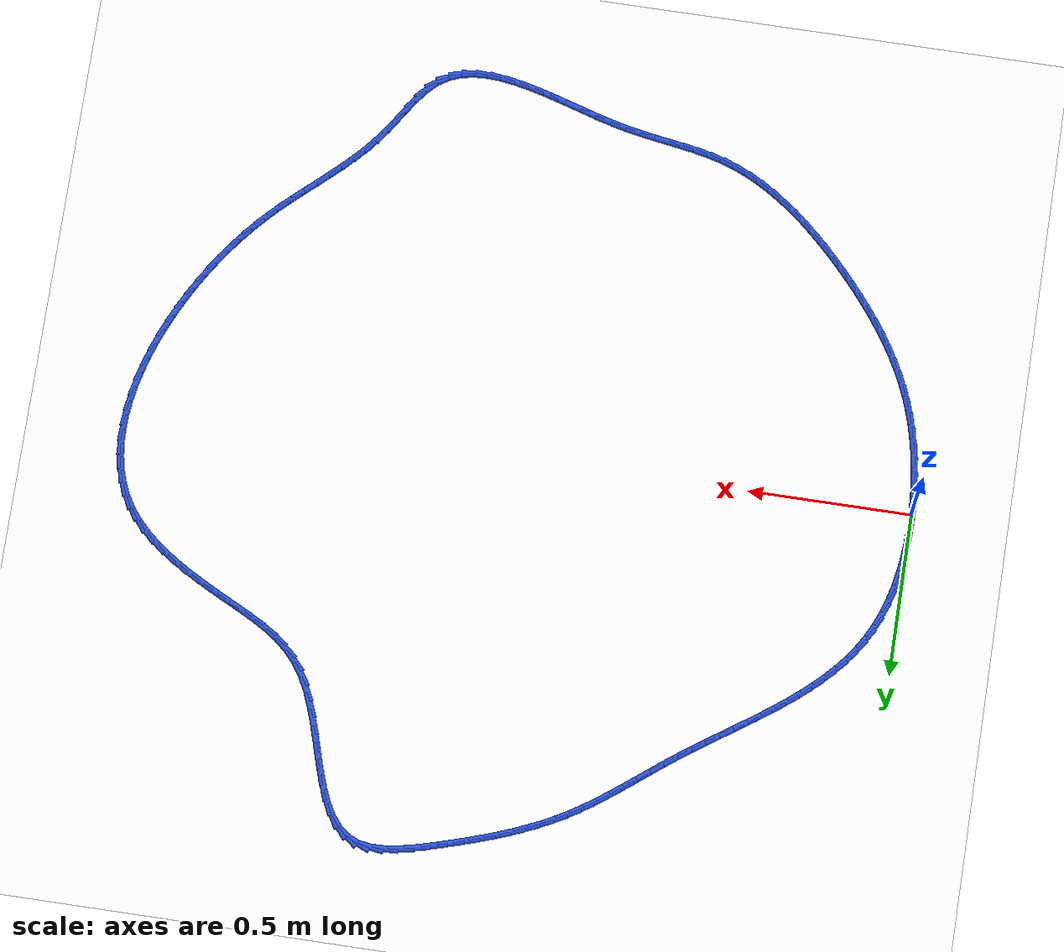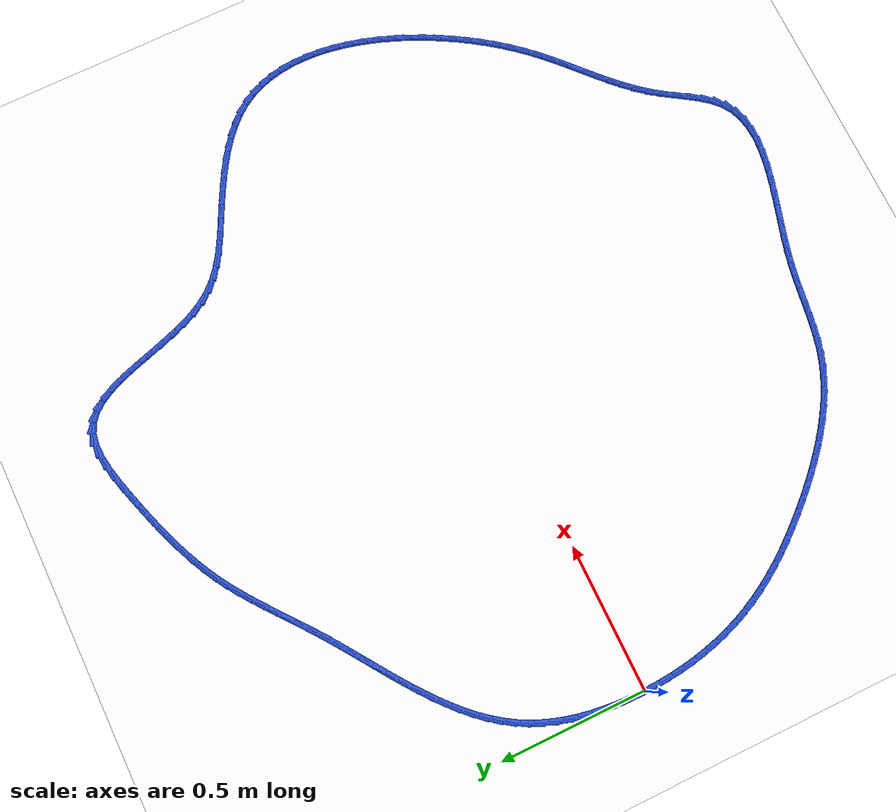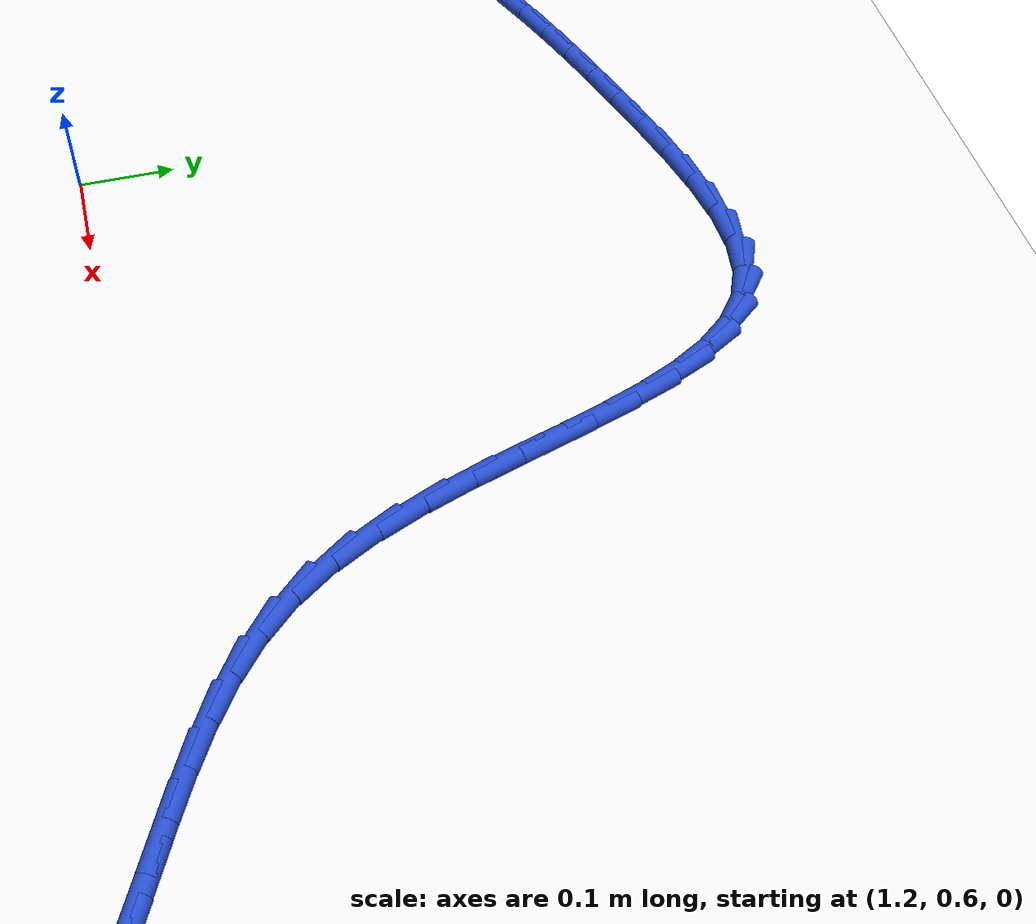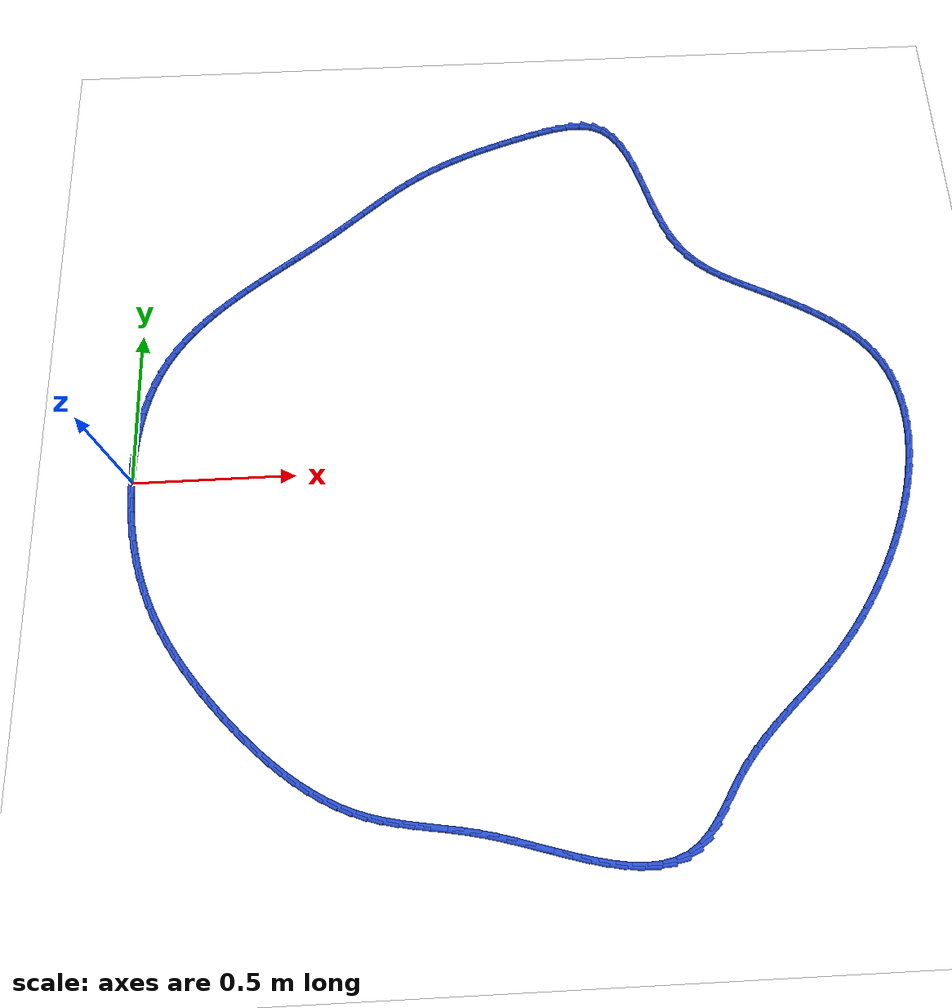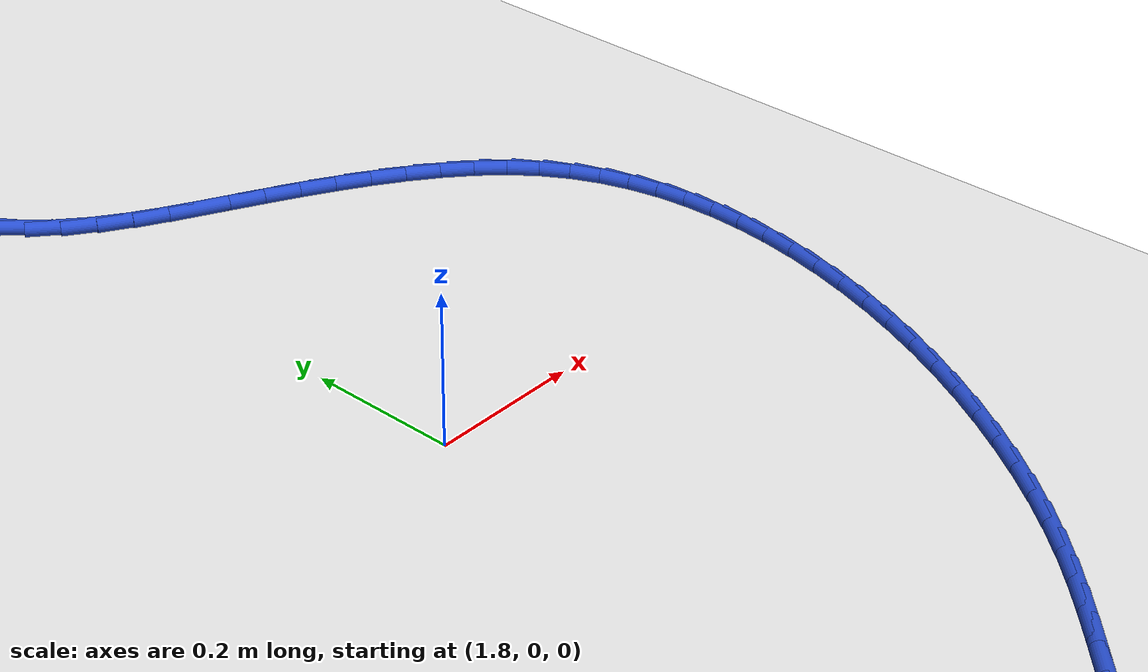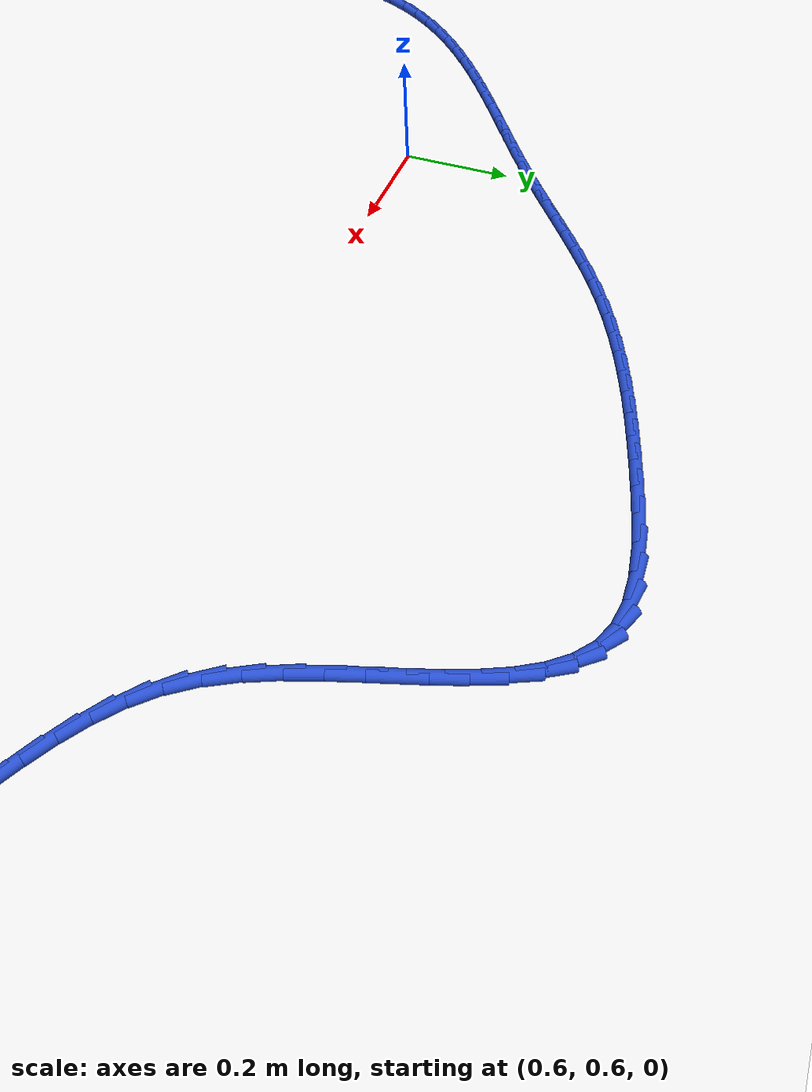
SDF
<sdf version="1.6">
 <world name="default">
  <light name="sun" type="directional">
   <pose>0 0 10 0 -0 0</pose>
   <diffuse>0.8 0.8 0.8 1</diffuse>
   <specular>0.2 0.2 0.2 1</specular>
   <attenuation>
    <range>1000</range>
    <constant>0.9</constant>
    <linear>0.01</linear>
    <quadratic>0.001</quadratic>
   </attenuation>
   <direction>-0.5 0.1 -0.9</direction>
  </light>
  <model name="ground_plane">
   <static>1</static>
   <link name="link">
    <collision name="collision">
     <geometry><plane><normal>0 0 1</normal><size>100 100</size></plane></geometry>
     <surface><friction><ode><mu>100</mu><mu2>50</mu2></ode></friction></surface>
    </collision>
    <visual name="visual">
     <cast_shadows>0</cast_shadows>
     <geometry><plane><normal>0 0 1</normal><size>100 100</size></plane></geometry>
     <material>
      <script><uri>file://media/materials/scripts/gazebo.material</uri><name>Gazebo/WhiteGlow</name></script>
     </material>
    </visual>
   </link>
  </model>
  <gravity>0 0 -9.8</gravity>
  <magnetic_field>6e-06 2.3e-05 -4.2e-05</magnetic_field>
  <atmosphere type="adiabatic"/>
  <physics name="default_physics" default="0" type="ode">
   <max_step_size>0.001</max_step_size>
   <real_time_factor>1</real_time_factor>
   <real_time_update_rate>1000</real_time_update_rate>
  </physics>
  <scene><ambient>0.4 0.4 0.4 1</ambient><background>0.7 0.7 0.7 1</background><shadows>1</shadows></scene>
  <spherical_coordinates>
   <surface_model>EARTH_WGS84</surface_model>
   <latitude_deg>0</latitude_deg>
   <longitude_deg>0</longitude_deg>
   <elevation>0</elevation>
   <heading_deg>0</heading_deg>
  </spherical_coordinates>
  <model name="line">
   <link name="link_0">
    <pose>-3.209238430557093e-17 9.71445146547012e-17 0.01 0 1.57 1.5660977608102957</pose>
    <collision name="collision">
     <geometry><cylinder><radius>0.01</radius><length>0.08</length></cylinder></geometry>
    </collision>
    <visual name="visual">
     <material>
      <script><name>Gazebo/Blue</name><uri>file://media/materials/scripts/gazebo.material</uri></script>
     </material>
     <geometry><cylinder><radius>0.01</radius><length>0.08</length></cylinder></geometry>
    </visual>
   </link>
   <link name="link_1">
    <pose>0.00021987925278518322 0.046796753615262934 0.01 0 1.57 1.524984169871335</pose>
    <collision name="collision">
     <geometry><cylinder><radius>0.01</radius><length>0.08</length></cylinder></geometry>
    </collision>
    <visual name="visual">
     <material>
      <script><name>Gazebo/Blue</name><uri>file://media/materials/scripts/gazebo.material</uri></script>
     </material>
     <geometry><cylinder><radius>0.01</radius><length>0.08</length></cylinder></geometry>
    </visual>
   </link>
   <link name="link_2">
    <pose>0.002365007465326923 0.09358842307314467 0.01 0 1.57 1.480142805591467</pose>
    <collision name="collision">
     <geometry><cylinder><radius>0.01</radius><length>0.08</length></cylinder></geometry>
    </collision>
    <visual name="visual">
     <material>
      <script><name>Gazebo/Blue</name><uri>file://media/materials/scripts/gazebo.material</uri></script>
     </material>
     <geometry><cylinder><radius>0.01</radius><length>0.08</length></cylinder></geometry>
    </visual>
   </link>
   <link name="link_3">
    <pose>0.006593358067236434 0.14010356387969447 0.01 0 1.57 1.4309719699759842</pose>
    <collision name="collision">
     <geometry><cylinder><radius>0.01</radius><length>0.08</length></cylinder></geometry>
    </collision>
    <visual name="visual">
     <material>
      <script><name>Gazebo/Blue</name><uri>file://media/materials/scripts/gazebo.material</uri></script>
     </material>
     <geometry><cylinder><radius>0.01</radius><length>0.08</length></cylinder></geometry>
    </visual>
   </link>
   <link name="link_4">
    <pose>0.013062904488124982 0.18607073154096132 0.01 0 1.57 1.3768284861886906</pose>
    <collision name="collision">
     <geometry><cylinder><radius>0.01</radius><length>0.08</length></cylinder></geometry>
    </collision>
    <visual name="visual">
     <material>
      <script><name>Gazebo/Blue</name><uri>file://media/materials/scripts/gazebo.material</uri></script>
     </material>
     <geometry><cylinder><radius>0.01</radius><length>0.08</length></cylinder></geometry>
    </visual>
   </link>
   <link name="link_5">
    <pose>0.021931620157603825 0.23121848156299446 0.01 0 1.57 1.3170434919180674</pose>
    <collision name="collision">
     <geometry><cylinder><radius>0.01</radius><length>0.08</length></cylinder></geometry>
    </collision>
    <visual name="visual">
     <material>
      <script><name>Gazebo/Blue</name><uri>file://media/materials/scripts/gazebo.material</uri></script>
     </material>
     <geometry><cylinder><radius>0.01</radius><length>0.08</length></cylinder></geometry>
    </visual>
   </link>
   <link name="link_6">
    <pose>0.03335747850528421 0.27527536945184294 0.01 0 1.57 1.2509558311294542</pose>
    <collision name="collision">
     <geometry><cylinder><radius>0.01</radius><length>0.08</length></cylinder></geometry>
    </collision>
    <visual name="visual">
     <material>
      <script><name>Gazebo/Blue</name><uri>file://media/materials/scripts/gazebo.material</uri></script>
     </material>
     <geometry><cylinder><radius>0.01</radius><length>0.08</length></cylinder></geometry>
    </visual>
   </link>
   <link name="link_7">
    <pose>0.0474984529607774 0.3179699507135559 0.01 0 1.57 1.1779702136256727</pose>
    <collision name="collision">
     <geometry><cylinder><radius>0.01</radius><length>0.08</length></cylinder></geometry>
    </collision>
    <visual name="visual">
     <material>
      <script><name>Gazebo/Blue</name><uri>file://media/materials/scripts/gazebo.material</uri></script>
     </material>
     <geometry><cylinder><radius>0.01</radius><length>0.08</length></cylinder></geometry>
    </visual>
   </link>
   <link name="link_8">
    <pose>0.06451251695369466 0.35903078085418244 0.01 0 1.57 1.0977892139822525</pose>
    <collision name="collision">
     <geometry><cylinder><radius>0.01</radius><length>0.08</length></cylinder></geometry>
    </collision>
    <visual name="visual">
     <material>
      <script><name>Gazebo/Blue</name><uri>file://media/materials/scripts/gazebo.material</uri></script>
     </material>
     <geometry><cylinder><radius>0.01</radius><length>0.08</length></cylinder></geometry>
    </visual>
   </link>
   <link name="link_9">
    <pose>0.08455308652895717 0.3981912776954497 0.01 0 1.57 1.0159182845645283</pose>
    <collision name="collision">
     <geometry><cylinder><radius>0.01</radius><length>0.08</length></cylinder></geometry>
    </collision>
    <visual name="visual">
     <material>
      <script><name>Gazebo/Blue</name><uri>file://media/materials/scripts/gazebo.material</uri></script>
     </material>
     <geometry><cylinder><radius>0.01</radius><length>0.08</length></cylinder></geometry>
    </visual>
   </link>
   <link name="link_10">
    <pose>0.10759871725954913 0.43537141930623646 0.01 0 1.57 0.9404009729480616</pose>
    <collision name="collision">
     <geometry><cylinder><radius>0.01</radius><length>0.08</length></cylinder></geometry>
    </collision>
    <visual name="visual">
     <material>
      <script><name>Gazebo/Blue</name><uri>file://media/materials/scripts/gazebo.material</uri></script>
     </material>
     <geometry><cylinder><radius>0.01</radius><length>0.08</length></cylinder></geometry>
    </visual>
   </link>
   <link name="link_11">
    <pose>0.13340214096680447 0.4707321171948322 0.01 0 1.57 0.8725580928074215</pose>
    <collision name="collision">
     <geometry><cylinder><radius>0.01</radius><length>0.08</length></cylinder></geometry>
    </collision>
    <visual name="visual">
     <material>
      <script><name>Gazebo/Blue</name><uri>file://media/materials/scripts/gazebo.material</uri></script>
     </material>
     <geometry><cylinder><radius>0.01</radius><length>0.08</length></cylinder></geometry>
    </visual>
   </link>
   <link name="link_12">
    <pose>0.16170112995800667 0.5044502433127732 0.01 0 1.57 0.8127880864573401</pose>
    <collision name="collision">
     <geometry><cylinder><radius>0.01</radius><length>0.08</length></cylinder></geometry>
    </collision>
    <visual name="visual">
     <material>
      <script><name>Gazebo/Blue</name><uri>file://media/materials/scripts/gazebo.material</uri></script>
     </material>
     <geometry><cylinder><radius>0.01</radius><length>0.08</length></cylinder></geometry>
    </visual>
   </link>
   <link name="link_13">
    <pose>0.19223345654043916 0.5367026696115959 0.01 0 1.57 0.7611409089183374</pose>
    <collision name="collision">
     <geometry><cylinder><radius>0.01</radius><length>0.08</length></cylinder></geometry>
    </collision>
    <visual name="visual">
     <material>
      <script><name>Gazebo/Blue</name><uri>file://media/materials/scripts/gazebo.material</uri></script>
     </material>
     <geometry><cylinder><radius>0.01</radius><length>0.08</length></cylinder></geometry>
    </visual>
   </link>
   <link name="link_14">
    <pose>0.22473689302138564 0.5676662680428365 0.01 0 1.57 0.7174354564988649</pose>
    <collision name="collision">
     <geometry><cylinder><radius>0.01</radius><length>0.08</length></cylinder></geometry>
    </collision>
    <visual name="visual">
     <material>
      <script><name>Gazebo/Blue</name><uri>file://media/materials/scripts/gazebo.material</uri></script>
     </material>
     <geometry><cylinder><radius>0.01</radius><length>0.08</length></cylinder></geometry>
    </visual>
   </link>
   <link name="link_15">
    <pose>0.25894921170812946 0.5975179105580316 0.01 0 1.57 0.6813638303788668</pose>
    <collision name="collision">
     <geometry><cylinder><radius>0.01</radius><length>0.08</length></cylinder></geometry>
    </collision>
    <visual name="visual">
     <material>
      <script><name>Gazebo/Blue</name><uri>file://media/materials/scripts/gazebo.material</uri></script>
     </material>
     <geometry><cylinder><radius>0.01</radius><length>0.08</length></cylinder></geometry>
    </visual>
   </link>
   <link name="link_16">
    <pose>0.2946081849079543 0.6264344691087173 0.01 0 1.57 0.6525722355664001</pose>
    <collision name="collision">
     <geometry><cylinder><radius>0.01</radius><length>0.08</length></cylinder></geometry>
    </collision>
    <visual name="visual">
     <material>
      <script><name>Gazebo/Blue</name><uri>file://media/materials/scripts/gazebo.material</uri></script>
     </material>
     <geometry><cylinder><radius>0.01</radius><length>0.08</length></cylinder></geometry>
    </visual>
   </link>
   <link name="link_17">
    <pose>0.3314515849281436 0.6545928156464298 0.01 0 1.57 0.6307179911545647</pose>
    <collision name="collision">
     <geometry><cylinder><radius>0.01</radius><length>0.08</length></cylinder></geometry>
    </collision>
    <visual name="visual">
     <material>
      <script><name>Gazebo/Blue</name><uri>file://media/materials/scripts/gazebo.material</uri></script>
     </material>
     <geometry><cylinder><radius>0.01</radius><length>0.08</length></cylinder></geometry>
    </visual>
   </link>
   <link name="link_18">
    <pose>0.36921718407598075 0.6821698221227059 0.01 0 1.57 0.615506718576898</pose>
    <collision name="collision">
     <geometry><cylinder><radius>0.01</radius><length>0.08</length></cylinder></geometry>
    </collision>
    <visual name="visual">
     <material>
      <script><name>Gazebo/Blue</name><uri>file://media/materials/scripts/gazebo.material</uri></script>
     </material>
     <geometry><cylinder><radius>0.01</radius><length>0.08</length></cylinder></geometry>
    </visual>
   </link>
   <link name="link_19">
    <pose>0.40764275465874933 0.7093423604890817 0.01 0 1.57 0.606714913238149</pose>
    <collision name="collision">
     <geometry><cylinder><radius>0.01</radius><length>0.08</length></cylinder></geometry>
    </collision>
    <visual name="visual">
     <material>
      <script><name>Gazebo/Blue</name><uri>file://media/materials/scripts/gazebo.material</uri></script>
     </material>
     <geometry><cylinder><radius>0.01</radius><length>0.08</length></cylinder></geometry>
    </visual>
   </link>
   <link name="link_20">
    <pose>0.4464660689837332 0.7362873026970937 0.01 0 1.57 0.6042024837390428</pose>
    <collision name="collision">
     <geometry><cylinder><radius>0.01</radius><length>0.08</length></cylinder></geometry>
    </collision>
    <visual name="visual">
     <material>
      <script><name>Gazebo/Blue</name><uri>file://media/materials/scripts/gazebo.material</uri></script>
     </material>
     <geometry><cylinder><radius>0.01</radius><length>0.08</length></cylinder></geometry>
    </visual>
   </link>
   <link name="link_21">
    <pose>0.48542489935821537 0.7631815206982783 0.01 0 1.57 0.6079185684136864</pose>
    <collision name="collision">
     <geometry><cylinder><radius>0.01</radius><length>0.08</length></cylinder></geometry>
    </collision>
    <visual name="visual">
     <material>
      <script><name>Gazebo/Blue</name><uri>file://media/materials/scripts/gazebo.material</uri></script>
     </material>
     <geometry><cylinder><radius>0.01</radius><length>0.08</length></cylinder></geometry>
    </visual>
   </link>
   <link name="link_22">
    <pose>0.5242570180894797 0.7902018864441716 0.01 0 1.57 0.6179025495465913</pose>
    <collision name="collision">
     <geometry><cylinder><radius>0.01</radius><length>0.08</length></cylinder></geometry>
    </collision>
    <visual name="visual">
     <material>
      <script><name>Gazebo/Blue</name><uri>file://media/materials/scripts/gazebo.material</uri></script>
     </material>
     <geometry><cylinder><radius>0.01</radius><length>0.08</length></cylinder></geometry>
    </visual>
   </link>
   <link name="link_23">
    <pose>0.5627001974848096 0.8175252718863099 0.01 0 1.57 0.6342452499665662</pose>
    <collision name="collision">
     <geometry><cylinder><radius>0.01</radius><length>0.08</length></cylinder></geometry>
    </collision>
    <visual name="visual">
     <material>
      <script><name>Gazebo/Blue</name><uri>file://media/materials/scripts/gazebo.material</uri></script>
     </material>
     <geometry><cylinder><radius>0.01</radius><length>0.08</length></cylinder></geometry>
    </visual>
   </link>
   <link name="link_24">
    <pose>0.6004933769158011 0.8453273336555412 0.01 0 1.57 0.6526459985040423</pose>
    <collision name="collision">
     <geometry><cylinder><radius>0.01</radius><length>0.08</length></cylinder></geometry>
    </collision>
    <visual name="visual">
     <material>
      <script><name>Gazebo/Blue</name><uri>file://media/materials/scripts/gazebo.material</uri></script>
     </material>
     <geometry><cylinder><radius>0.01</radius><length>0.08</length></cylinder></geometry>
    </visual>
   </link>
   <link name="link_25">
    <pose>0.6375217776997384 0.8736313978957929 0.01 0 1.57 0.6643143220982112</pose>
    <collision name="collision">
     <geometry><cylinder><radius>0.01</radius><length>0.08</length></cylinder></geometry>
    </collision>
    <visual name="visual">
     <material>
      <script><name>Gazebo/Blue</name><uri>file://media/materials/scripts/gazebo.material</uri></script>
     </material>
     <geometry><cylinder><radius>0.01</radius><length>0.08</length></cylinder></geometry>
    </visual>
   </link>
   <link name="link_26">
    <pose>0.6739574894532931 0.9021620608734133 0.01 0 1.57 0.6680812171025552</pose>
    <collision name="collision">
     <geometry><cylinder><radius>0.01</radius><length>0.08</length></cylinder></geometry>
    </collision>
    <visual name="visual">
     <material>
      <script><name>Gazebo/Blue</name><uri>file://media/materials/scripts/gazebo.material</uri></script>
     </material>
     <geometry><cylinder><radius>0.01</radius><length>0.08</length></cylinder></geometry>
    </visual>
   </link>
   <link name="link_27">
    <pose>0.7100059506109205 0.9306091911128742 0.01 0 1.57 0.6637679730141532</pose>
    <collision name="collision">
     <geometry><cylinder><radius>0.01</radius><length>0.08</length></cylinder></geometry>
    </collision>
    <visual name="visual">
     <material>
      <script><name>Gazebo/Blue</name><uri>file://media/materials/scripts/gazebo.material</uri></script>
     </material>
     <geometry><cylinder><radius>0.01</radius><length>0.08</length></cylinder></geometry>
    </visual>
   </link>
   <link name="link_28">
    <pose>0.745872599607075 0.9586626571386466 0.01 0 1.57 0.6511595499071906</pose>
    <collision name="collision">
     <geometry><cylinder><radius>0.01</radius><length>0.08</length></cylinder></geometry>
    </collision>
    <visual name="visual">
     <material>
      <script><name>Gazebo/Blue</name><uri>file://media/materials/scripts/gazebo.material</uri></script>
     </material>
     <geometry><cylinder><radius>0.01</radius><length>0.08</length></cylinder></geometry>
    </visual>
   </link>
   <link name="link_29">
    <pose>0.7817628748762113 0.9860123274752021 0.01 0 1.57 0.6300108527167803</pose>
    <collision name="collision">
     <geometry><cylinder><radius>0.01</radius><length>0.08</length></cylinder></geometry>
    </collision>
    <visual name="visual">
     <material>
      <script><name>Gazebo/Blue</name><uri>file://media/materials/scripts/gazebo.material</uri></script>
     </material>
     <geometry><cylinder><radius>0.01</radius><length>0.08</length></cylinder></geometry>
    </visual>
   </link>
   <link name="link_30">
    <pose>0.8178822148527845 1.0123480706470118 0.01 0 1.57 0.6000718335855401</pose>
    <collision name="collision">
     <geometry><cylinder><radius>0.01</radius><length>0.08</length></cylinder></geometry>
    </collision>
    <visual name="visual">
     <material>
      <script><name>Gazebo/Blue</name><uri>file://media/materials/scripts/gazebo.material</uri></script>
     </material>
     <geometry><cylinder><radius>0.01</radius><length>0.08</length></cylinder></geometry>
    </visual>
   </link>
   <link name="link_31">
    <pose>0.8544360579712497 1.0373597551785478 0.01 0 1.57 0.5611900027718707</pose>
    <collision name="collision">
     <geometry><cylinder><radius>0.01</radius><length>0.08</length></cylinder></geometry>
    </collision>
    <visual name="visual">
     <material>
      <script><name>Gazebo/Blue</name><uri>file://media/materials/scripts/gazebo.material</uri></script>
     </material>
     <geometry><cylinder><radius>0.01</radius><length>0.08</length></cylinder></geometry>
    </visual>
   </link>
   <link name="link_32">
    <pose>0.8916292328618419 1.0607397020099958 0.01 0 1.57 0.517305601322966</pose>
    <collision name="collision">
     <geometry><cylinder><radius>0.01</radius><length>0.08</length></cylinder></geometry>
    </collision>
    <visual name="visual">
     <material>
      <script><name>Gazebo/Blue</name><uri>file://media/materials/scripts/gazebo.material</uri></script>
     </material>
     <geometry><cylinder><radius>0.01</radius><length>0.08</length></cylinder></geometry>
    </visual>
   </link>
   <link name="link_33">
    <pose>0.9296224959135643 1.08235747496298 0.01 0 1.57 0.475473525729647</pose>
    <collision name="collision">
     <geometry><cylinder><radius>0.01</radius><length>0.08</length></cylinder></geometry>
    </collision>
    <visual name="visual">
     <material>
      <script><name>Gazebo/Blue</name><uri>file://media/materials/scripts/gazebo.material</uri></script>
     </material>
     <geometry><cylinder><radius>0.01</radius><length>0.08</length></cylinder></geometry>
    </visual>
   </link>
   <link name="link_34">
    <pose>0.9685036007317257 1.1023762290941839 0.01 0 1.57 0.4369134625742217</pose>
    <collision name="collision">
     <geometry><cylinder><radius>0.01</radius><length>0.08</length></cylinder></geometry>
    </collision>
    <visual name="visual">
     <material>
      <script><name>Gazebo/Blue</name><uri>file://media/materials/scripts/gazebo.material</uri></script>
     </material>
     <geometry><cylinder><radius>0.01</radius><length>0.08</length></cylinder></geometry>
    </visual>
   </link>
   <link name="link_35">
    <pose>1.0083534389453437 1.1209867158886937 0.01 0 1.57 0.40209219930529816</pose>
    <collision name="collision">
     <geometry><cylinder><radius>0.01</radius><length>0.08</length></cylinder></geometry>
    </collision>
    <visual name="visual">
     <material>
      <script><name>Gazebo/Blue</name><uri>file://media/materials/scripts/gazebo.material</uri></script>
     </material>
     <geometry><cylinder><radius>0.01</radius><length>0.08</length></cylinder></geometry>
    </visual>
   </link>
   <link name="link_36">
    <pose>1.0492529021834383 1.138379686831598 0.01 0 1.57 0.37132965152351044</pose>
    <collision name="collision">
     <geometry><cylinder><radius>0.01</radius><length>0.08</length></cylinder></geometry>
    </collision>
    <visual name="visual">
     <material>
      <script><name>Gazebo/Blue</name><uri>file://media/materials/scripts/gazebo.material</uri></script>
     </material>
     <geometry><cylinder><radius>0.01</radius><length>0.08</length></cylinder></geometry>
    </visual>
   </link>
   <link name="link_37">
    <pose>1.0912828820750284 1.1547458934079846 0.01 0 1.57 0.3448039044892352</pose>
    <collision name="collision">
     <geometry><cylinder><radius>0.01</radius><length>0.08</length></cylinder></geometry>
    </collision>
    <visual name="visual">
     <material>
      <script><name>Gazebo/Blue</name><uri>file://media/materials/scripts/gazebo.material</uri></script>
     </material>
     <geometry><cylinder><radius>0.01</radius><length>0.08</length></cylinder></geometry>
    </visual>
   </link>
   <link name="link_38">
    <pose>1.134524270249133 1.1702760871029407 0.01 0 1.57 0.32256617867204873</pose>
    <collision name="collision">
     <geometry><cylinder><radius>0.01</radius><length>0.08</length></cylinder></geometry>
    </collision>
    <visual name="visual">
     <material>
      <script><name>Gazebo/Blue</name><uri>file://media/materials/scripts/gazebo.material</uri></script>
     </material>
     <geometry><cylinder><radius>0.01</radius><length>0.08</length></cylinder></geometry>
    </visual>
   </link>
   <link name="link_39">
    <pose>1.1790579583347713 1.185161019401555 0.01 0 1.57 0.30456135553817776</pose>
    <collision name="collision">
     <geometry><cylinder><radius>0.01</radius><length>0.08</length></cylinder></geometry>
    </collision>
    <visual name="visual">
     <material>
      <script><name>Gazebo/Blue</name><uri>file://media/materials/scripts/gazebo.material</uri></script>
     </material>
     <geometry><cylinder><radius>0.01</radius><length>0.08</length></cylinder></geometry>
    </visual>
   </link>
   <link name="link_40">
    <pose>1.2249648379609612 1.1995914417889133 0.01 0 1.57 0.290543775917738</pose>
    <collision name="collision">
     <geometry><cylinder><radius>0.01</radius><length>0.08</length></cylinder></geometry>
    </collision>
    <visual name="visual">
     <material>
      <script><name>Gazebo/Blue</name><uri>file://media/materials/scripts/gazebo.material</uri></script>
     </material>
     <geometry><cylinder><radius>0.01</radius><length>0.08</length></cylinder></geometry>
    </visual>
   </link>
   <link name="link_41">
    <pose>1.2723204834304094 1.2137510204459803 0.01 0 1.57 0.2707269464709753</pose>
    <collision name="collision">
     <geometry><cylinder><radius>0.01</radius><length>0.08</length></cylinder></geometry>
    </collision>
    <visual name="visual">
     <material>
      <script><name>Gazebo/Blue</name><uri>file://media/materials/scripts/gazebo.material</uri></script>
     </material>
     <geometry><cylinder><radius>0.01</radius><length>0.08</length></cylinder></geometry>
    </visual>
   </link>
   <link name="link_42">
    <pose>1.3207206325180272 1.2271840423753106 0.01 0 1.57 0.22664085976437714</pose>
    <collision name="collision">
     <geometry><cylinder><radius>0.01</radius><length>0.08</length></cylinder></geometry>
    </collision>
    <visual name="visual">
     <material>
      <script><name>Gazebo/Blue</name><uri>file://media/materials/scripts/gazebo.material</uri></script>
     </material>
     <geometry><cylinder><radius>0.01</radius><length>0.08</length></cylinder></geometry>
    </visual>
   </link>
   <link name="link_43">
    <pose>1.3689062204849374 1.2382957755650505 0.01 0 1.57 0.1506635015036484</pose>
    <collision name="collision">
     <geometry><cylinder><radius>0.01</radius><length>0.08</length></cylinder></geometry>
    </collision>
    <visual name="visual">
     <material>
      <script><name>Gazebo/Blue</name><uri>file://media/materials/scripts/gazebo.material</uri></script>
     </material>
     <geometry><cylinder><radius>0.01</radius><length>0.08</length></cylinder></geometry>
    </visual>
   </link>
   <link name="link_44">
    <pose>1.4155299408277586 1.2453739064028986 0.01 0 1.57 0.03046589268835789</pose>
    <collision name="collision">
     <geometry><cylinder><radius>0.01</radius><length>0.08</length></cylinder></geometry>
    </collision>
    <visual name="visual">
     <material>
      <script><name>Gazebo/Blue</name><uri>file://media/materials/scripts/gazebo.material</uri></script>
     </material>
     <geometry><cylinder><radius>0.01</radius><length>0.08</length></cylinder></geometry>
    </visual>
   </link>
   <link name="link_45">
    <pose>1.4592444870431112 1.2467061212765564 0.01 0 1.57 -0.15402413808957333</pose>
    <collision name="collision">
     <geometry><cylinder><radius>0.01</radius><length>0.08</length></cylinder></geometry>
    </collision>
    <visual name="visual">
     <material>
      <script><name>Gazebo/Blue</name><uri>file://media/materials/scripts/gazebo.material</uri></script>
     </material>
     <geometry><cylinder><radius>0.01</radius><length>0.08</length></cylinder></geometry>
    </visual>
   </link>
   <link name="link_46">
    <pose>1.4987025526276134 1.2405801065737239 0.01 0 1.57 -0.41623954469186025</pose>
    <collision name="collision">
     <geometry><cylinder><radius>0.01</radius><length>0.08</length></cylinder></geometry>
    </collision>
    <visual name="visual">
     <material>
      <script><name>Gazebo/Blue</name><uri>file://media/materials/scripts/gazebo.material</uri></script>
     </material>
     <geometry><cylinder><radius>0.01</radius><length>0.08</length></cylinder></geometry>
    </visual>
   </link>
   <link name="link_47">
    <pose>1.5327425325763862 1.225532063020155 0.01 0 1.57 -0.6857853250750617</pose>
    <collision name="collision">
     <geometry><cylinder><radius>0.01</radius><length>0.08</length></cylinder></geometry>
    </collision>
    <visual name="visual">
     <material>
      <script><name>Gazebo/Blue</name><uri>file://media/materials/scripts/gazebo.material</uri></script>
     </material>
     <geometry><cylinder><radius>0.01</radius><length>0.08</length></cylinder></geometry>
    </visual>
   </link>
   <link name="link_48">
    <pose>1.561577166524245 1.2019374029319543 0.01 0 1.57 -0.9018696962709747</pose>
    <collision name="collision">
     <geometry><cylinder><radius>0.01</radius><length>0.08</length></cylinder></geometry>
    </collision>
    <visual name="visual">
     <material>
      <script><name>Gazebo/Blue</name><uri>file://media/materials/scripts/gazebo.material</uri></script>
     </material>
     <geometry><cylinder><radius>0.01</radius><length>0.08</length></cylinder></geometry>
    </visual>
   </link>
   <link name="link_49">
    <pose>1.5860359215479582 1.1709968718251904 0.01 0 1.57 -1.0572442836678682</pose>
    <collision name="collision">
     <geometry><cylinder><radius>0.01</radius><length>0.08</length></cylinder></geometry>
    </collision>
    <visual name="visual">
     <material>
      <script><name>Gazebo/Blue</name><uri>file://media/materials/scripts/gazebo.material</uri></script>
     </material>
     <geometry><cylinder><radius>0.01</radius><length>0.08</length></cylinder></geometry>
    </visual>
   </link>
   <link name="link_50">
    <pose>1.60695118975501 1.1339151296273804 0.01 0 1.57 -1.1619637105951606</pose>
    <collision name="collision">
     <geometry><cylinder><radius>0.01</radius><length>0.08</length></cylinder></geometry>
    </collision>
    <visual name="visual">
     <material>
      <script><name>Gazebo/Blue</name><uri>file://media/materials/scripts/gazebo.material</uri></script>
     </material>
     <geometry><cylinder><radius>0.01</radius><length>0.08</length></cylinder></geometry>
    </visual>
   </link>
   <link name="link_51">
    <pose>1.6251553632528846 1.0918968362660415 0.01 0 1.57 -1.2280414936706172</pose>
    <collision name="collision">
     <geometry><cylinder><radius>0.01</radius><length>0.08</length></cylinder></geometry>
    </collision>
    <visual name="visual">
     <material>
      <script><name>Gazebo/Blue</name><uri>file://media/materials/scripts/gazebo.material</uri></script>
     </material>
     <geometry><cylinder><radius>0.01</radius><length>0.08</length></cylinder></geometry>
    </visual>
   </link>
   <link name="link_52">
    <pose>1.6414808341490663 1.0461466516686926 0.01 0 1.57 -1.2642835738913443</pose>
    <collision name="collision">
     <geometry><cylinder><radius>0.01</radius><length>0.08</length></cylinder></geometry>
    </collision>
    <visual name="visual">
     <material>
      <script><name>Gazebo/Blue</name><uri>file://media/materials/scripts/gazebo.material</uri></script>
     </material>
     <geometry><cylinder><radius>0.01</radius><length>0.08</length></cylinder></geometry>
    </visual>
   </link>
   <link name="link_53">
    <pose>1.6567599945510394 0.99786923576285 0.01 0 1.57 -1.2759166459129523</pose>
    <collision name="collision">
     <geometry><cylinder><radius>0.01</radius><length>0.08</length></cylinder></geometry>
    </collision>
    <visual name="visual">
     <material>
      <script><name>Gazebo/Blue</name><uri>file://media/materials/scripts/gazebo.material</uri></script>
     </material>
     <geometry><cylinder><radius>0.01</radius><length>0.08</length></cylinder></geometry>
    </visual>
   </link>
   <link name="link_54">
    <pose>1.671825236566288 0.948269248476033 0.01 0 1.57 -1.2652224332716555</pose>
    <collision name="collision">
     <geometry><cylinder><radius>0.01</radius><length>0.08</length></cylinder></geometry>
    </collision>
    <visual name="visual">
     <material>
      <script><name>Gazebo/Blue</name><uri>file://media/materials/scripts/gazebo.material</uri></script>
     </material>
     <geometry><cylinder><radius>0.01</radius><length>0.08</length></cylinder></geometry>
    </visual>
   </link>
   <link name="link_55">
    <pose>1.6875089523022955 0.8985513497357576 0.01 0 1.57 -1.2320405548048965</pose>
    <collision name="collision">
     <geometry><cylinder><radius>0.01</radius><length>0.08</length></cylinder></geometry>
    </collision>
    <visual name="visual">
     <material>
      <script><name>Gazebo/Blue</name><uri>file://media/materials/scripts/gazebo.material</uri></script>
     </material>
     <geometry><cylinder><radius>0.01</radius><length>0.08</length></cylinder></geometry>
    </visual>
   </link>
   <link name="link_56">
    <pose>1.7046435338665473 0.8499201994695419 0.01 0 1.57 -1.1739913810581275</pose>
    <collision name="collision">
     <geometry><cylinder><radius>0.01</radius><length>0.08</length></cylinder></geometry>
    </collision>
    <visual name="visual">
     <material>
      <script><name>Gazebo/Blue</name><uri>file://media/materials/scripts/gazebo.material</uri></script>
     </material>
     <geometry><cylinder><radius>0.01</radius><length>0.08</length></cylinder></geometry>
    </visual>
   </link>
   <link name="link_57">
    <pose>1.7240613733665273 0.8035804576049044 0.01 0 1.57 -1.0866074532054473</pose>
    <collision name="collision">
     <geometry><cylinder><radius>0.01</radius><length>0.08</length></cylinder></geometry>
    </collision>
    <visual name="visual">
     <material>
      <script><name>Gazebo/Blue</name><uri>file://media/materials/scripts/gazebo.material</uri></script>
     </material>
     <geometry><cylinder><radius>0.01</radius><length>0.08</length></cylinder></geometry>
    </visual>
   </link>
   <link name="link_58">
    <pose>1.7465948629097192 0.7607367840693616 0.01 0 1.57 -0.9642002316851017</pose>
    <collision name="collision">
     <geometry><cylinder><radius>0.01</radius><length>0.08</length></cylinder></geometry>
    </collision>
    <visual name="visual">
     <material>
      <script><name>Gazebo/Blue</name><uri>file://media/materials/scripts/gazebo.material</uri></script>
     </material>
     <geometry><cylinder><radius>0.01</radius><length>0.08</length></cylinder></geometry>
    </visual>
   </link>
   <link name="link_59">
    <pose>1.7730686460825404 0.7225826564292347 0.01 0 1.57 -0.8220209030377961</pose>
    <collision name="collision">
     <geometry><cylinder><radius>0.01</radius><length>0.08</length></cylinder></geometry>
    </collision>
    <visual name="visual">
     <material>
      <script><name>Gazebo/Blue</name><uri>file://media/materials/scripts/gazebo.material</uri></script>
     </material>
     <geometry><cylinder><radius>0.01</radius><length>0.08</length></cylinder></geometry>
    </visual>
   </link>
   <link name="link_60">
    <pose>1.8037739502809733 0.6895417469604594 0.01 0 1.57 -0.6968834012175427</pose>
    <collision name="collision">
     <geometry><cylinder><radius>0.01</radius><length>0.08</length></cylinder></geometry>
    </collision>
    <visual name="visual">
     <material>
      <script><name>Gazebo/Blue</name><uri>file://media/materials/scripts/gazebo.material</uri></script>
     </material>
     <geometry><cylinder><radius>0.01</radius><length>0.08</length></cylinder></geometry>
    </visual>
   </link>
   <link name="link_61">
    <pose>1.8381332089725082 0.6607839186725879 0.01 0 1.57 -0.5975100795253664</pose>
    <collision name="collision">
     <geometry><cylinder><radius>0.01</radius><length>0.08</length></cylinder></geometry>
    </collision>
    <visual name="visual">
     <material>
      <script><name>Gazebo/Blue</name><uri>file://media/materials/scripts/gazebo.material</uri></script>
     </material>
     <geometry><cylinder><radius>0.01</radius><length>0.08</length></cylinder></geometry>
    </visual>
   </link>
   <link name="link_62">
    <pose>1.87548898683961 0.6353637710823283 0.01 0 1.57 -0.5256751692671261</pose>
    <collision name="collision">
     <geometry><cylinder><radius>0.01</radius><length>0.08</length></cylinder></geometry>
    </collision>
    <visual name="visual">
     <material>
      <script><name>Gazebo/Blue</name><uri>file://media/materials/scripts/gazebo.material</uri></script>
     </material>
     <geometry><cylinder><radius>0.01</radius><length>0.08</length></cylinder></geometry>
    </visual>
   </link>
   <link name="link_63">
    <pose>1.9151838485647434 0.6123359037063872 0.01 0 1.57 -0.4807589113709854</pose>
    <collision name="collision">
     <geometry><cylinder><radius>0.01</radius><length>0.08</length></cylinder></geometry>
    </collision>
    <visual name="visual">
     <material>
      <script><name>Gazebo/Blue</name><uri>file://media/materials/scripts/gazebo.material</uri></script>
     </material>
     <geometry><cylinder><radius>0.01</radius><length>0.08</length></cylinder></geometry>
    </visual>
   </link>
   <link name="link_64">
    <pose>1.9565603588303722 0.5907549160614726 0.01 0 1.57 -0.46136479738933345</pose>
    <collision name="collision">
     <geometry><cylinder><radius>0.01</radius><length>0.08</length></cylinder></geometry>
    </collision>
    <visual name="visual">
     <material>
      <script><name>Gazebo/Blue</name><uri>file://media/materials/scripts/gazebo.material</uri></script>
     </material>
     <geometry><cylinder><radius>0.01</radius><length>0.08</length></cylinder></geometry>
    </visual>
   </link>
   <link name="link_65">
    <pose>1.9989610823189607 0.569675407664291 0.01 0 1.57 -0.4640747519650512</pose>
    <collision name="collision">
     <geometry><cylinder><radius>0.01</radius><length>0.08</length></cylinder></geometry>
    </collision>
    <visual name="visual">
     <material>
      <script><name>Gazebo/Blue</name><uri>file://media/materials/scripts/gazebo.material</uri></script>
     </material>
     <geometry><cylinder><radius>0.01</radius><length>0.08</length></cylinder></geometry>
    </visual>
   </link>
   <link name="link_66">
    <pose>2.041745859973644 0.5482601699347459 0.01 0 1.57 -0.478686622693304</pose>
    <collision name="collision">
     <geometry><cylinder><radius>0.01</radius><length>0.08</length></cylinder></geometry>
    </collision>
    <visual name="visual">
     <material>
      <script><name>Gazebo/Blue</name><uri>file://media/materials/scripts/gazebo.material</uri></script>
     </material>
     <geometry><cylinder><radius>0.01</radius><length>0.08</length></cylinder></geometry>
    </visual>
   </link>
   <link name="link_67">
    <pose>2.084350952636455 0.5261505709050018 0.01 0 1.57 -0.5027474010741864</pose>
    <collision name="collision">
     <geometry><cylinder><radius>0.01</radius><length>0.08</length></cylinder></geometry>
    </collision>
    <visual name="visual">
     <material>
      <script><name>Gazebo/Blue</name><uri>file://media/materials/scripts/gazebo.material</uri></script>
     </material>
     <geometry><cylinder><radius>0.01</radius><length>0.08</length></cylinder></geometry>
    </visual>
   </link>
   <link name="link_68">
    <pose>2.126233744352673 0.503120261837042 0.01 0 1.57 -0.5369117692166184</pose>
    <collision name="collision">
     <geometry><cylinder><radius>0.01</radius><length>0.08</length></cylinder></geometry>
    </collision>
    <visual name="visual">
     <material>
      <script><name>Gazebo/Blue</name><uri>file://media/materials/scripts/gazebo.material</uri></script>
     </material>
     <geometry><cylinder><radius>0.01</radius><length>0.08</length></cylinder></geometry>
    </visual>
   </link>
   <link name="link_69">
    <pose>2.1668516198880976 0.47894289850510036 0.01 0 1.57 -0.5822222823168217</pose>
    <collision name="collision">
     <geometry><cylinder><radius>0.01</radius><length>0.08</length></cylinder></geometry>
    </collision>
    <visual name="visual">
     <material>
      <script><name>Gazebo/Blue</name><uri>file://media/materials/scripts/gazebo.material</uri></script>
     </material>
     <geometry><cylinder><radius>0.01</radius><length>0.08</length></cylinder></geometry>
    </visual>
   </link>
   <link name="link_70">
    <pose>2.2056619640085326 0.4533921366834104 0.01 0 1.57 -0.6400756904759483</pose>
    <collision name="collision">
     <geometry><cylinder><radius>0.01</radius><length>0.08</length></cylinder></geometry>
    </collision>
    <visual name="visual">
     <material>
      <script><name>Gazebo/Blue</name><uri>file://media/materials/scripts/gazebo.material</uri></script>
     </material>
     <geometry><cylinder><radius>0.01</radius><length>0.08</length></cylinder></geometry>
    </visual>
   </link>
   <link name="link_71">
    <pose>2.24212216147978 0.42624163214620503 0.01 0 1.57 -0.7121277651113456</pose>
    <collision name="collision">
     <geometry><cylinder><radius>0.01</radius><length>0.08</length></cylinder></geometry>
    </collision>
    <visual name="visual">
     <material>
      <script><name>Gazebo/Blue</name><uri>file://media/materials/scripts/gazebo.material</uri></script>
     </material>
     <geometry><cylinder><radius>0.01</radius><length>0.08</length></cylinder></geometry>
    </visual>
   </link>
   <link name="link_72">
    <pose>2.27568959706764 0.3972650406677183 0.01 0 1.57 -0.8000627157706809</pose>
    <collision name="collision">
     <geometry><cylinder><radius>0.01</radius><length>0.08</length></cylinder></geometry>
    </collision>
    <visual name="visual">
     <material>
      <script><name>Gazebo/Blue</name><uri>file://media/materials/scripts/gazebo.material</uri></script>
     </material>
     <geometry><cylinder><radius>0.01</radius><length>0.08</length></cylinder></geometry>
    </visual>
   </link>
   <link name="link_73">
    <pose>2.3058216555379154 0.36623601802218303 0.01 0 1.57 -0.9051306060898924</pose>
    <collision name="collision">
     <geometry><cylinder><radius>0.01</radius><length>0.08</length></cylinder></geometry>
    </collision>
    <visual name="visual">
     <material>
      <script><name>Gazebo/Blue</name><uri>file://media/materials/scripts/gazebo.material</uri></script>
     </material>
     <geometry><cylinder><radius>0.01</radius><length>0.08</length></cylinder></geometry>
    </visual>
   </link>
   <link name="link_74">
    <pose>2.3319757216564065 0.33292821998383343 0.01 0 1.57 -1.0241737372253812</pose>
    <collision name="collision">
     <geometry><cylinder><radius>0.01</radius><length>0.08</length></cylinder></geometry>
    </collision>
    <visual name="visual">
     <material>
      <script><name>Gazebo/Blue</name><uri>file://media/materials/scripts/gazebo.material</uri></script>
     </material>
     <geometry><cylinder><radius>0.01</radius><length>0.08</length></cylinder></geometry>
    </visual>
   </link>
   <link name="link_75">
    <pose>2.353723091190348 0.29718702118522117 0.01 0 1.57 -1.141833159732061</pose>
    <collision name="collision">
     <geometry><cylinder><radius>0.01</radius><length>0.08</length></cylinder></geometry>
    </collision>
    <visual name="visual">
     <material>
      <script><name>Gazebo/Blue</name><uri>file://media/materials/scripts/gazebo.material</uri></script>
     </material>
     <geometry><cylinder><radius>0.01</radius><length>0.08</length></cylinder></geometry>
    </visual>
   </link>
   <link name="link_76">
    <pose>2.3711153097674162 0.2591601636445422 0.01 0 1.57 -1.2523396371162494</pose>
    <collision name="collision">
     <geometry><cylinder><radius>0.01</radius><length>0.08</length></cylinder></geometry>
    </collision>
    <visual name="visual">
     <material>
      <script><name>Gazebo/Blue</name><uri>file://media/materials/scripts/gazebo.material</uri></script>
     </material>
     <geometry><cylinder><radius>0.01</radius><length>0.08</length></cylinder></geometry>
    </visual>
   </link>
   <link name="link_77">
    <pose>2.384330465536313 0.21907506109758382 0.01 0 1.57 -1.3543671681701592</pose>
    <collision name="collision">
     <geometry><cylinder><radius>0.01</radius><length>0.08</length></cylinder></geometry>
    </collision>
    <visual name="visual">
     <material>
      <script><name>Gazebo/Blue</name><uri>file://media/materials/scripts/gazebo.material</uri></script>
     </material>
     <geometry><cylinder><radius>0.01</radius><length>0.08</length></cylinder></geometry>
    </visual>
   </link>
   <link name="link_78">
    <pose>2.393546647292632 0.1771591276874206 0.01 0 1.57 -1.4474510270458563</pose>
    <collision name="collision">
     <geometry><cylinder><radius>0.01</radius><length>0.08</length></cylinder></geometry>
    </collision>
    <visual name="visual">
     <material>
      <script><name>Gazebo/Blue</name><uri>file://media/materials/scripts/gazebo.material</uri></script>
     </material>
     <geometry><cylinder><radius>0.01</radius><length>0.08</length></cylinder></geometry>
    </visual>
   </link>
   <link name="link_79">
    <pose>2.398941943831972 0.1336397775571293 0.01 0 1.57 -1.531780912013535</pose>
    <collision name="collision">
     <geometry><cylinder><radius>0.01</radius><length>0.08</length></cylinder></geometry>
    </collision>
    <visual name="visual">
     <material>
      <script><name>Gazebo/Blue</name><uri>file://media/materials/scripts/gazebo.material</uri></script>
     </material>
     <geometry><cylinder><radius>0.01</radius><length>0.08</length></cylinder></geometry>
    </visual>
   </link>
   <link name="link_80">
    <pose>2.400694443949929 0.08874442484978488 0.01 0 1.57 1.5336270730185173</pose>
    <collision name="collision">
     <geometry><cylinder><radius>0.01</radius><length>0.08</length></cylinder></geometry>
    </collision>
    <visual name="visual">
     <material>
      <script><name>Gazebo/Blue</name><uri>file://media/materials/scripts/gazebo.material</uri></script>
     </material>
     <geometry><cylinder><radius>0.01</radius><length>0.08</length></cylinder></geometry>
    </visual>
   </link>
   <link name="link_81">
    <pose>2.3989822364420994 0.04270048370846303 0.01 0 1.57 1.4647585450670022</pose>
    <collision name="collision">
     <geometry><cylinder><radius>0.01</radius><length>0.08</length></cylinder></geometry>
    </collision>
    <visual name="visual">
     <material>
      <script><name>Gazebo/Blue</name><uri>file://media/materials/scripts/gazebo.material</uri></script>
     </material>
     <geometry><cylinder><radius>0.01</radius><length>0.08</length></cylinder></geometry>
    </visual>
   </link>
   <link name="link_82">
    <pose>2.393983410104081 -0.004264631723761472 0.01 0 1.57 1.4022971191299147</pose>
    <collision name="collision">
     <geometry><cylinder><radius>0.01</radius><length>0.08</length></cylinder></geometry>
    </collision>
    <visual name="visual">
     <material>
      <script><name>Gazebo/Blue</name><uri>file://media/materials/scripts/gazebo.material</uri></script>
     </material>
     <geometry><cylinder><radius>0.01</radius><length>0.08</length></cylinder></geometry>
    </visual>
   </link>
   <link name="link_83">
    <pose>2.3858760537314687 -0.05192350730381144 0.01 0 1.57 1.3453398802391077</pose>
    <collision name="collision">
     <geometry><cylinder><radius>0.01</radius><length>0.08</length></cylinder></geometry>
    </collision>
    <visual name="visual">
     <material>
      <script><name>Gazebo/Blue</name><uri>file://media/materials/scripts/gazebo.material</uri></script>
     </material>
     <geometry><cylinder><radius>0.01</radius><length>0.08</length></cylinder></geometry>
    </visual>
   </link>
   <link name="link_84">
    <pose>2.374838256119861 -0.10004872888861199 0.01 0 1.57 1.293035429502675</pose>
    <collision name="collision">
     <geometry><cylinder><radius>0.01</radius><length>0.08</length></cylinder></geometry>
    </collision>
    <visual name="visual">
     <material>
      <script><name>Gazebo/Blue</name><uri>file://media/materials/scripts/gazebo.material</uri></script>
     </material>
     <geometry><cylinder><radius>0.01</radius><length>0.08</length></cylinder></geometry>
    </visual>
   </link>
   <link name="link_85">
    <pose>2.361048106064852 -0.14841288233508756 0.01 0 1.57 1.2446024082311242</pose>
    <collision name="collision">
     <geometry><cylinder><radius>0.01</radius><length>0.08</length></cylinder></geometry>
    </collision>
    <visual name="visual">
     <material>
      <script><name>Gazebo/Blue</name><uri>file://media/materials/scripts/gazebo.material</uri></script>
     </material>
     <geometry><cylinder><radius>0.01</radius><length>0.08</length></cylinder></geometry>
    </visual>
   </link>
   <link name="link_86">
    <pose>2.34468369236204 -0.19678855350016256 0.01 0 1.57 1.1993318355117164</pose>
    <collision name="collision">
     <geometry><cylinder><radius>0.01</radius><length>0.08</length></cylinder></geometry>
    </collision>
    <visual name="visual">
     <material>
      <script><name>Gazebo/Blue</name><uri>file://media/materials/scripts/gazebo.material</uri></script>
     </material>
     <geometry><cylinder><radius>0.01</radius><length>0.08</length></cylinder></geometry>
    </visual>
   </link>
   <link name="link_87">
    <pose>2.3259231038070225 -0.24494832824076224 0.01 0 1.57 1.1565804175019712</pose>
    <collision name="collision">
     <geometry><cylinder><radius>0.01</radius><length>0.08</length></cylinder></geometry>
    </collision>
    <visual name="visual">
     <material>
      <script><name>Gazebo/Blue</name><uri>file://media/materials/scripts/gazebo.material</uri></script>
     </material>
     <geometry><cylinder><radius>0.01</radius><length>0.08</length></cylinder></geometry>
    </visual>
   </link>
   <link name="link_88">
    <pose>2.3049444291953938 -0.2926647924138093 0.01 0 1.57 1.1157591652181083</pose>
    <collision name="collision">
     <geometry><cylinder><radius>0.01</radius><length>0.08</length></cylinder></geometry>
    </collision>
    <visual name="visual">
     <material>
      <script><name>Gazebo/Blue</name><uri>file://media/materials/scripts/gazebo.material</uri></script>
     </material>
     <geometry><cylinder><radius>0.01</radius><length>0.08</length></cylinder></geometry>
    </visual>
   </link>
   <link name="link_89">
    <pose>2.2819257573227527 -0.339710531876229 0.01 0 1.57 1.0763196920658165</pose>
    <collision name="collision">
     <geometry><cylinder><radius>0.01</radius><length>0.08</length></cylinder></geometry>
    </collision>
    <visual name="visual">
     <material>
      <script><name>Gazebo/Blue</name><uri>file://media/materials/scripts/gazebo.material</uri></script>
     </material>
     <geometry><cylinder><radius>0.01</radius><length>0.08</length></cylinder></geometry>
    </visual>
   </link>
   <link name="link_90">
    <pose>2.2570451769846938 -0.3858581324849456 0.01 0 1.57 1.037739283660254</pose>
    <collision name="collision">
     <geometry><cylinder><radius>0.01</radius><length>0.08</length></cylinder></geometry>
    </collision>
    <visual name="visual">
     <material>
      <script><name>Gazebo/Blue</name><uri>file://media/materials/scripts/gazebo.material</uri></script>
     </material>
     <geometry><cylinder><radius>0.01</radius><length>0.08</length></cylinder></geometry>
    </visual>
   </link>
   <link name="link_91">
    <pose>2.2304807769768153 -0.4308801800968838 0.01 0 1.57 0.9995050182316088</pose>
    <collision name="collision">
     <geometry><cylinder><radius>0.01</radius><length>0.08</length></cylinder></geometry>
    </collision>
    <visual name="visual">
     <material>
      <script><name>Gazebo/Blue</name><uri>file://media/materials/scripts/gazebo.material</uri></script>
     </material>
     <geometry><cylinder><radius>0.01</radius><length>0.08</length></cylinder></geometry>
    </visual>
   </link>
   <link name="link_92">
    <pose>2.2024106460947124 -0.4745492605689684 0.01 0 1.57 0.9610966809648012</pose>
    <collision name="collision">
     <geometry><cylinder><radius>0.01</radius><length>0.08</length></cylinder></geometry>
    </collision>
    <visual name="visual">
     <material>
      <script><name>Gazebo/Blue</name><uri>file://media/materials/scripts/gazebo.material</uri></script>
     </material>
     <geometry><cylinder><radius>0.01</radius><length>0.08</length></cylinder></geometry>
    </visual>
   </link>
   <link name="link_93">
    <pose>2.1730128731339837 -0.5166379597581225 0.01 0 1.57 0.9219678278052561</pose>
    <collision name="collision">
     <geometry><cylinder><radius>0.01</radius><length>0.08</length></cylinder></geometry>
    </collision>
    <visual name="visual">
     <material>
      <script><name>Gazebo/Blue</name><uri>file://media/materials/scripts/gazebo.material</uri></script>
     </material>
     <geometry><cylinder><radius>0.01</radius><length>0.08</length></cylinder></geometry>
    </visual>
   </link>
   <link name="link_94">
    <pose>2.142465546890225 -0.5569188635212712 0.01 0 1.57 0.8815240277991248</pose>
    <collision name="collision">
     <geometry><cylinder><radius>0.01</radius><length>0.08</length></cylinder></geometry>
    </collision>
    <visual name="visual">
     <material>
      <script><name>Gazebo/Blue</name><uri>file://media/materials/scripts/gazebo.material</uri></script>
     </material>
     <geometry><cylinder><radius>0.01</radius><length>0.08</length></cylinder></geometry>
    </visual>
   </link>
   <link name="link_95">
    <pose>2.1109467561590316 -0.5951645577153388 0.01 0 1.57 0.8392224958088419</pose>
    <collision name="collision">
     <geometry><cylinder><radius>0.01</radius><length>0.08</length></cylinder></geometry>
    </collision>
    <visual name="visual">
     <material>
      <script><name>Gazebo/Blue</name><uri>file://media/materials/scripts/gazebo.material</uri></script>
     </material>
     <geometry><cylinder><radius>0.01</radius><length>0.08</length></cylinder></geometry>
    </visual>
   </link>
   <link name="link_96">
    <pose>2.078635164351534 -0.6311560730018434 0.01 0 1.57 0.7991823153461424</pose>
    <collision name="collision">
     <geometry><cylinder><radius>0.01</radius><length>0.08</length></cylinder></geometry>
    </collision>
    <visual name="visual">
     <material>
      <script><name>Gazebo/Blue</name><uri>file://media/materials/scripts/gazebo.material</uri></script>
     </material>
     <geometry><cylinder><radius>0.01</radius><length>0.08</length></cylinder></geometry>
    </visual>
   </link>
   <link name="link_97">
    <pose>2.045730282410615 -0.6649808246111214 0.01 0 1.57 0.7679508410412292</pose>
    <collision name="collision">
     <geometry><cylinder><radius>0.01</radius><length>0.08</length></cylinder></geometry>
    </collision>
    <visual name="visual">
     <material>
      <script><name>Gazebo/Blue</name><uri>file://media/materials/scripts/gazebo.material</uri></script>
     </material>
     <geometry><cylinder><radius>0.01</radius><length>0.08</length></cylinder></geometry>
    </visual>
   </link>
   <link name="link_98">
    <pose>2.012457870834085 -0.69711200286961 0.01 0 1.57 0.7469213424556508</pose>
    <collision name="collision">
     <geometry><cylinder><radius>0.01</radius><length>0.08</length></cylinder></geometry>
    </collision>
    <visual name="visual">
     <material>
      <script><name>Gazebo/Blue</name><uri>file://media/materials/scripts/gazebo.material</uri></script>
     </material>
     <geometry><cylinder><radius>0.01</radius><length>0.08</length></cylinder></geometry>
    </visual>
   </link>
   <link name="link_99">
    <pose>1.979045363152527 -0.7280473857351213 0.01 0 1.57 0.7368573172017987</pose>
    <collision name="collision">
     <geometry><cylinder><radius>0.01</radius><length>0.08</length></cylinder></geometry>
    </collision>
    <visual name="visual">
     <material>
      <script><name>Gazebo/Blue</name><uri>file://media/materials/scripts/gazebo.material</uri></script>
     </material>
     <geometry><cylinder><radius>0.01</radius><length>0.08</length></cylinder></geometry>
    </visual>
   </link>
   <link name="link_100">
    <pose>1.945720192896527 -0.7582847511654686 0.01 0 1.57 0.7382738378833245</pose>
    <collision name="collision">
     <geometry><cylinder><radius>0.01</radius><length>0.08</length></cylinder></geometry>
    </collision>
    <visual name="visual">
     <material>
      <script><name>Gazebo/Blue</name><uri>file://media/materials/scripts/gazebo.material</uri></script>
     </material>
     <geometry><cylinder><radius>0.01</radius><length>0.08</length></cylinder></geometry>
    </visual>
   </link>
   <link name="link_101">
    <pose>1.9127097935966695 -0.7883218771184656 0.01 0 1.57 0.7514393562236549</pose>
    <collision name="collision">
     <geometry><cylinder><radius>0.01</radius><length>0.08</length></cylinder></geometry>
    </collision>
    <visual name="visual">
     <material>
      <script><name>Gazebo/Blue</name><uri>file://media/materials/scripts/gazebo.material</uri></script>
     </material>
     <geometry><cylinder><radius>0.01</radius><length>0.08</length></cylinder></geometry>
    </visual>
   </link>
   <link name="link_102">
    <pose>1.8802415987835408 -0.8186565415519242 0.01 0 1.57 0.7763487660284082</pose>
    <collision name="collision">
     <geometry><cylinder><radius>0.01</radius><length>0.08</length></cylinder></geometry>
    </collision>
    <visual name="visual">
     <material>
      <script><name>Gazebo/Blue</name><uri>file://media/materials/scripts/gazebo.material</uri></script>
     </material>
     <geometry><cylinder><radius>0.01</radius><length>0.08</length></cylinder></geometry>
    </visual>
   </link>
   <link name="link_103">
    <pose>1.8485430419877242 -0.8497865224236574 0.01 0 1.57 0.8126643075136382</pose>
    <collision name="collision">
     <geometry><cylinder><radius>0.01</radius><length>0.08</length></cylinder></geometry>
    </collision>
    <visual name="visual">
     <material>
      <script><name>Gazebo/Blue</name><uri>file://media/materials/scripts/gazebo.material</uri></script>
     </material>
     <geometry><cylinder><radius>0.01</radius><length>0.08</length></cylinder></geometry>
    </visual>
   </link>
   <link name="link_104">
    <pose>1.8178415567398052 -0.8822095976914786 0.01 0 1.57 0.8596357708084238</pose>
    <collision name="collision">
     <geometry><cylinder><radius>0.01</radius><length>0.08</length></cylinder></geometry>
    </collision>
    <visual name="visual">
     <material>
      <script><name>Gazebo/Blue</name><uri>file://media/materials/scripts/gazebo.material</uri></script>
     </material>
     <geometry><cylinder><radius>0.01</radius><length>0.08</length></cylinder></geometry>
    </visual>
   </link>
   <link name="link_105">
    <pose>1.78836457657037 -0.9164235453132009 0.01 0 1.57 0.916028699389244</pose>
    <collision name="collision">
     <geometry><cylinder><radius>0.01</radius><length>0.08</length></cylinder></geometry>
    </collision>
    <visual name="visual">
     <material>
      <script><name>Gazebo/Blue</name><uri>file://media/materials/scripts/gazebo.material</uri></script>
     </material>
     <geometry><cylinder><radius>0.01</radius><length>0.08</length></cylinder></geometry>
    </visual>
   </link>
   <link name="link_106">
    <pose>1.7603395350100006 -0.9529261432466372 0.01 0 1.57 0.9752520746618075</pose>
    <collision name="collision">
     <geometry><cylinder><radius>0.01</radius><length>0.08</length></cylinder></geometry>
    </collision>
    <visual name="visual">
     <material>
      <script><name>Gazebo/Blue</name><uri>file://media/materials/scripts/gazebo.material</uri></script>
     </material>
     <geometry><cylinder><radius>0.01</radius><length>0.08</length></cylinder></geometry>
    </visual>
   </link>
   <link name="link_107">
    <pose>1.7338785094102986 -0.9919763552666984 0.01 0 1.57 1.001900429665724</pose>
    <collision name="collision">
     <geometry><cylinder><radius>0.01</radius><length>0.08</length></cylinder></geometry>
    </collision>
    <visual name="visual">
     <material>
      <script><name>Gazebo/Blue</name><uri>file://media/materials/scripts/gazebo.material</uri></script>
     </material>
     <geometry><cylinder><radius>0.01</radius><length>0.08</length></cylinder></geometry>
    </visual>
   </link>
   <link name="link_108">
    <pose>1.7082420163151608 -1.0320702157563146 0.01 0 1.57 0.9821417638700723</pose>
    <collision name="collision">
     <geometry><cylinder><radius>0.01</radius><length>0.08</length></cylinder></geometry>
    </collision>
    <visual name="visual">
     <material>
      <script><name>Gazebo/Blue</name><uri>file://media/materials/scripts/gazebo.material</uri></script>
     </material>
     <geometry><cylinder><radius>0.01</radius><length>0.08</length></cylinder></geometry>
    </visual>
   </link>
   <link name="link_109">
    <pose>1.6823092885888988 -1.0709144129949484 0.01 0 1.57 0.9115580403140892</pose>
    <collision name="collision">
     <geometry><cylinder><radius>0.01</radius><length>0.08</length></cylinder></geometry>
    </collision>
    <visual name="visual">
     <material>
      <script><name>Gazebo/Blue</name><uri>file://media/materials/scripts/gazebo.material</uri></script>
     </material>
     <geometry><cylinder><radius>0.01</radius><length>0.08</length></cylinder></geometry>
    </visual>
   </link>
   <link name="link_110">
    <pose>1.654957768895657 -1.106211929130372 0.01 0 1.57 0.7780002135769051</pose>
    <collision name="collision">
     <geometry><cylinder><radius>0.01</radius><length>0.08</length></cylinder></geometry>
    </collision>
    <visual name="visual">
     <material>
      <script><name>Gazebo/Blue</name><uri>file://media/materials/scripts/gazebo.material</uri></script>
     </material>
     <geometry><cylinder><radius>0.01</radius><length>0.08</length></cylinder></geometry>
    </visual>
   </link>
   <link name="link_111">
    <pose>1.6250648998995771 -1.1356657463103574 0.01 0 1.57 0.5789534486509589</pose>
    <collision name="collision">
     <geometry><cylinder><radius>0.01</radius><length>0.08</length></cylinder></geometry>
    </collision>
    <visual name="visual">
     <material>
      <script><name>Gazebo/Blue</name><uri>file://media/materials/scripts/gazebo.material</uri></script>
     </material>
     <geometry><cylinder><radius>0.01</radius><length>0.08</length></cylinder></geometry>
    </visual>
   </link>
   <link name="link_112">
    <pose>1.5917346601065365 -1.1574528472814076 0.01 0 1.57 0.37374849686089145</pose>
    <collision name="collision">
     <geometry><cylinder><radius>0.01</radius><length>0.08</length></cylinder></geometry>
    </collision>
    <visual name="visual">
     <material>
      <script><name>Gazebo/Blue</name><uri>file://media/materials/scripts/gazebo.material</uri></script>
     </material>
     <geometry><cylinder><radius>0.01</radius><length>0.08</length></cylinder></geometry>
    </visual>
   </link>
   <link name="link_113">
    <pose>1.5550666238930033 -1.1718333864203851 0.01 0 1.57 0.19447474367327164</pose>
    <collision name="collision">
     <geometry><cylinder><radius>0.01</radius><length>0.08</length></cylinder></geometry>
    </collision>
    <visual name="visual">
     <material>
      <script><name>Gazebo/Blue</name><uri>file://media/materials/scripts/gazebo.material</uri></script>
     </material>
     <geometry><cylinder><radius>0.01</radius><length>0.08</length></cylinder></geometry>
    </visual>
   </link>
   <link name="link_114">
    <pose>1.5154337921336538 -1.1796396320922413 0.01 0 1.57 0.04884815083030801</pose>
    <collision name="collision">
     <geometry><cylinder><radius>0.01</radius><length>0.08</length></cylinder></geometry>
    </collision>
    <visual name="visual">
     <material>
      <script><name>Gazebo/Blue</name><uri>file://media/materials/scripts/gazebo.material</uri></script>
     </material>
     <geometry><cylinder><radius>0.01</radius><length>0.08</length></cylinder></geometry>
    </visual>
   </link>
   <link name="link_115">
    <pose>1.4732091733931194 -1.1817038687522907 0.01 0 1.57 -0.063937717175047</pose>
    <collision name="collision">
     <geometry><cylinder><radius>0.01</radius><length>0.08</length></cylinder></geometry>
    </collision>
    <visual name="visual">
     <material>
      <script><name>Gazebo/Blue</name><uri>file://media/materials/scripts/gazebo.material</uri></script>
     </material>
     <geometry><cylinder><radius>0.01</radius><length>0.08</length></cylinder></geometry>
    </visual>
   </link>
   <link name="link_116">
    <pose>1.4287657762360308 -1.1788583808558468 0.01 0 1.57 -0.14845791535402425</pose>
    <collision name="collision">
     <geometry><cylinder><radius>0.01</radius><length>0.08</length></cylinder></geometry>
    </collision>
    <visual name="visual">
     <material>
      <script><name>Gazebo/Blue</name><uri>file://media/materials/scripts/gazebo.material</uri></script>
     </material>
     <geometry><cylinder><radius>0.01</radius><length>0.08</length></cylinder></geometry>
    </visual>
   </link>
   <link name="link_117">
    <pose>1.382476609227021 -1.171935452858224 0.01 0 1.57 -0.20975944924102316</pose>
    <collision name="collision">
     <geometry><cylinder><radius>0.01</radius><length>0.08</length></cylinder></geometry>
    </collision>
    <visual name="visual">
     <material>
      <script><name>Gazebo/Blue</name><uri>file://media/materials/scripts/gazebo.material</uri></script>
     </material>
     <geometry><cylinder><radius>0.01</radius><length>0.08</length></cylinder></geometry>
    </visual>
   </link>
   <link name="link_118">
    <pose>1.334714680930722 -1.1617673692147368 0.01 0 1.57 -0.25200712322696717</pose>
    <collision name="collision">
     <geometry><cylinder><radius>0.01</radius><length>0.08</length></cylinder></geometry>
    </collision>
    <visual name="visual">
     <material>
      <script><name>Gazebo/Blue</name><uri>file://media/materials/scripts/gazebo.material</uri></script>
     </material>
     <geometry><cylinder><radius>0.01</radius><length>0.08</length></cylinder></geometry>
    </visual>
   </link>
   <link name="link_119">
    <pose>1.2858529999117643 -1.149186414380699 0.01 0 1.57 -0.27817697864029944</pose>
    <collision name="collision">
     <geometry><cylinder><radius>0.01</radius><length>0.08</length></cylinder></geometry>
    </collision>
    <visual name="visual">
     <material>
      <script><name>Gazebo/Blue</name><uri>file://media/materials/scripts/gazebo.material</uri></script>
     </material>
     <geometry><cylinder><radius>0.01</radius><length>0.08</length></cylinder></geometry>
    </visual>
   </link>
   <link name="link_120">
    <pose>1.2362645747347794 -1.1350248728114234 0.01 0 1.57 -0.29011885115252184</pose>
    <collision name="collision">
     <geometry><cylinder><radius>0.01</radius><length>0.08</length></cylinder></geometry>
    </collision>
    <visual name="visual">
     <material>
      <script><name>Gazebo/Blue</name><uri>file://media/materials/scripts/gazebo.material</uri></script>
     </material>
     <geometry><cylinder><radius>0.01</radius><length>0.08</length></cylinder></geometry>
    </visual>
   </link>
   <link name="link_121">
    <pose>1.1863224139643989 -1.1201150289622255 0.01 0 1.57 -0.28867948193971593</pose>
    <collision name="collision">
     <geometry><cylinder><radius>0.01</radius><length>0.08</length></cylinder></geometry>
    </collision>
    <visual name="visual">
     <material>
      <script><name>Gazebo/Blue</name><uri>file://media/materials/scripts/gazebo.material</uri></script>
     </material>
     <geometry><cylinder><radius>0.01</radius><length>0.08</length></cylinder></geometry>
    </visual>
   </link>
   <link name="link_122">
    <pose>1.1363995261652557 -1.105289167288419 0.01 0 1.57 -0.2737766030665136</pose>
    <collision name="collision">
     <geometry><cylinder><radius>0.01</radius><length>0.08</length></cylinder></geometry>
    </collision>
    <visual name="visual">
     <material>
      <script><name>Gazebo/Blue</name><uri>file://media/materials/scripts/gazebo.material</uri></script>
     </material>
     <geometry><cylinder><radius>0.01</radius><length>0.08</length></cylinder></geometry>
    </visual>
   </link>
   <link name="link_123">
    <pose>1.0868689199019808 -1.0913795722453183 0.01 0 1.57 -0.244395076603305</pose>
    <collision name="collision">
     <geometry><cylinder><radius>0.01</radius><length>0.08</length></cylinder></geometry>
    </collision>
    <visual name="visual">
     <material>
      <script><name>Gazebo/Blue</name><uri>file://media/materials/scripts/gazebo.material</uri></script>
     </material>
     <geometry><cylinder><radius>0.01</radius><length>0.08</length></cylinder></geometry>
    </visual>
   </link>
   <link name="link_124">
    <pose>1.0381035891265695 -1.0792184726082201 0.01 0 1.57 -0.20451830565084816</pose>
    <collision name="collision">
     <geometry><cylinder><radius>0.01</radius><length>0.08</length></cylinder></geometry>
    </collision>
    <visual name="visual">
     <material>
      <script><name>Gazebo/Blue</name><uri>file://media/materials/scripts/gazebo.material</uri></script>
     </material>
     <geometry><cylinder><radius>0.01</radius><length>0.08</length></cylinder></geometry>
    </visual>
   </link>
   <link name="link_125">
    <pose>0.9903937211513518 -1.0693225705670852 0.01 0 1.57 -0.17342223580335903</pose>
    <collision name="collision">
     <geometry><cylinder><radius>0.01</radius><length>0.08</length></cylinder></geometry>
    </collision>
    <visual name="visual">
     <material>
      <script><name>Gazebo/Blue</name><uri>file://media/materials/scripts/gazebo.material</uri></script>
     </material>
     <geometry><cylinder><radius>0.01</radius><length>0.08</length></cylinder></geometry>
    </visual>
   </link>
   <link name="link_126">
    <pose>0.9437521683988003 -1.0611518108930984 0.01 0 1.57 -0.15668211391233047</pose>
    <collision name="collision">
     <geometry><cylinder><radius>0.01</radius><length>0.08</length></cylinder></geometry>
    </collision>
    <visual name="visual">
     <material>
      <script><name>Gazebo/Blue</name><uri>file://media/materials/scripts/gazebo.material</uri></script>
     </material>
     <geometry><cylinder><radius>0.01</radius><length>0.08</length></cylinder></geometry>
    </visual>
   </link>
   <link name="link_127">
    <pose>0.898133789139475 -1.0539451573250433 0.01 0 1.57 -0.15562054507566536</pose>
    <collision name="collision">
     <geometry><cylinder><radius>0.01</radius><length>0.08</length></cylinder></geometry>
    </collision>
    <visual name="visual">
     <material>
      <script><name>Gazebo/Blue</name><uri>file://media/materials/scripts/gazebo.material</uri></script>
     </material>
     <geometry><cylinder><radius>0.01</radius><length>0.08</length></cylinder></geometry>
    </visual>
   </link>
   <link name="link_128">
    <pose>0.8534934416439338 -1.0469415736017027 0.01 0 1.57 -0.1713079939092948</pose>
    <collision name="collision">
     <geometry><cylinder><radius>0.01</radius><length>0.08</length></cylinder></geometry>
    </collision>
    <visual name="visual">
     <material>
      <script><name>Gazebo/Blue</name><uri>file://media/materials/scripts/gazebo.material</uri></script>
     </material>
     <geometry><cylinder><radius>0.01</radius><length>0.08</length></cylinder></geometry>
    </visual>
   </link>
   <link name="link_129">
    <pose>0.8097859841827351 -1.0393800234618602 0.01 0 1.57 -0.20449500703981588</pose>
    <collision name="collision">
     <geometry><cylinder><radius>0.01</radius><length>0.08</length></cylinder></geometry>
    </collision>
    <visual name="visual">
     <material>
      <script><name>Gazebo/Blue</name><uri>file://media/materials/scripts/gazebo.material</uri></script>
     </material>
     <geometry><cylinder><radius>0.01</radius><length>0.08</length></cylinder></geometry>
    </visual>
   </link>
   <link name="link_130">
    <pose>0.7669662750264378 -1.0304994706442987 0.01 0 1.57 -0.25540638852888436</pose>
    <collision name="collision">
     <geometry><cylinder><radius>0.01</radius><length>0.08</length></cylinder></geometry>
    </collision>
    <visual name="visual">
     <material>
      <script><name>Gazebo/Blue</name><uri>file://media/materials/scripts/gazebo.material</uri></script>
     </material>
     <geometry><cylinder><radius>0.01</radius><length>0.08</length></cylinder></geometry>
    </visual>
   </link>
   <link name="link_131">
    <pose>0.7249891724455995 -1.0195388788878017 0.01 0 1.57 -0.3231220298106022</pose>
    <collision name="collision">
     <geometry><cylinder><radius>0.01</radius><length>0.08</length></cylinder></geometry>
    </collision>
    <visual name="visual">
     <material>
      <script><name>Gazebo/Blue</name><uri>file://media/materials/scripts/gazebo.material</uri></script>
     </material>
     <geometry><cylinder><radius>0.01</radius><length>0.08</length></cylinder></geometry>
    </visual>
   </link>
   <link name="link_132">
    <pose>0.6838103501867854 -1.005749825237177 0.01 0 1.57 -0.39689461570212775</pose>
    <collision name="collision">
     <geometry><cylinder><radius>0.01</radius><length>0.08</length></cylinder></geometry>
    </collision>
    <visual name="visual">
     <material>
      <script><name>Gazebo/Blue</name><uri>file://media/materials/scripts/gazebo.material</uri></script>
     </material>
     <geometry><cylinder><radius>0.01</radius><length>0.08</length></cylinder></geometry>
    </visual>
   </link>
   <link name="link_133">
    <pose>0.643413548956668 -0.9888180100652127 0.01 0 1.57 -0.4648022665270589</pose>
    <collision name="collision">
     <geometry><cylinder><radius>0.01</radius><length>0.08</length></cylinder></geometry>
    </collision>
    <visual name="visual">
     <material>
      <script><name>Gazebo/Blue</name><uri>file://media/materials/scripts/gazebo.material</uri></script>
     </material>
     <geometry><cylinder><radius>0.01</radius><length>0.08</length></cylinder></geometry>
    </visual>
   </link>
   <link name="link_134">
    <pose>0.6038169959080758 -0.9689625499292708 0.01 0 1.57 -0.5263012586812306</pose>
    <collision name="collision">
     <geometry><cylinder><radius>0.01</radius><length>0.08</length></cylinder></geometry>
    </collision>
    <visual name="visual">
     <material>
      <script><name>Gazebo/Blue</name><uri>file://media/materials/scripts/gazebo.material</uri></script>
     </material>
     <geometry><cylinder><radius>0.01</radius><length>0.08</length></cylinder></geometry>
    </visual>
   </link>
   <link name="link_135">
    <pose>0.5650410346660959 -0.9464352977420937 0.01 0 1.57 -0.5817199676052025</pose>
    <collision name="collision">
     <geometry><cylinder><radius>0.01</radius><length>0.08</length></cylinder></geometry>
    </collision>
    <visual name="visual">
     <material>
      <script><name>Gazebo/Blue</name><uri>file://media/materials/scripts/gazebo.material</uri></script>
     </material>
     <geometry><cylinder><radius>0.01</radius><length>0.08</length></cylinder></geometry>
    </visual>
   </link>
   <link name="link_136">
    <pose>0.5271060088558145 -0.9214881064164229 0.01 0 1.57 -0.6314823520375271</pose>
    <collision name="collision">
     <geometry><cylinder><radius>0.01</radius><length>0.08</length></cylinder></geometry>
    </collision>
    <visual name="visual">
     <material>
      <script><name>Gazebo/Blue</name><uri>file://media/materials/scripts/gazebo.material</uri></script>
     </material>
     <geometry><cylinder><radius>0.01</radius><length>0.08</length></cylinder></geometry>
    </visual>
   </link>
   <link name="link_137">
    <pose>0.4900322621023204 -0.8943728288650024 0.01 0 1.57 -0.67605051905966</pose>
    <collision name="collision">
     <geometry><cylinder><radius>0.01</radius><length>0.08</length></cylinder></geometry>
    </collision>
    <visual name="visual">
     <material>
      <script><name>Gazebo/Blue</name><uri>file://media/materials/scripts/gazebo.material</uri></script>
     </material>
     <geometry><cylinder><radius>0.01</radius><length>0.08</length></cylinder></geometry>
    </visual>
   </link>
   <link name="link_138">
    <pose>0.4538401380306997 -0.8653413180005738 0.01 0 1.57 -0.7158855264017713</pose>
    <collision name="collision">
     <geometry><cylinder><radius>0.01</radius><length>0.08</length></cylinder></geometry>
    </collision>
    <visual name="visual">
     <material>
      <script><name>Gazebo/Blue</name><uri>file://media/materials/scripts/gazebo.material</uri></script>
     </material>
     <geometry><cylinder><radius>0.01</radius><length>0.08</length></cylinder></geometry>
    </visual>
   </link>
   <link name="link_139">
    <pose>0.4185499802660397 -0.8346454267358798 0.01 0 1.57 -0.7514227349607382</pose>
    <collision name="collision">
     <geometry><cylinder><radius>0.01</radius><length>0.08</length></cylinder></geometry>
    </collision>
    <visual name="visual">
     <material>
      <script><name>Gazebo/Blue</name><uri>file://media/materials/scripts/gazebo.material</uri></script>
     </material>
     <geometry><cylinder><radius>0.01</radius><length>0.08</length></cylinder></geometry>
    </visual>
   </link>
   <link name="link_140">
    <pose>0.3841821324334274 -0.8025370079836629 0.01 0 1.57 -0.7830576231646306</pose>
    <collision name="collision">
     <geometry><cylinder><radius>0.01</radius><length>0.08</length></cylinder></geometry>
    </collision>
    <visual name="visual">
     <material>
      <script><name>Gazebo/Blue</name><uri>file://media/materials/scripts/gazebo.material</uri></script>
     </material>
     <geometry><cylinder><radius>0.01</radius><length>0.08</length></cylinder></geometry>
    </visual>
   </link>
   <link name="link_141">
    <pose>0.3507569381579492 -0.7692679146566646 0.01 0 1.57 -0.8111385005696273</pose>
    <collision name="collision">
     <geometry><cylinder><radius>0.01</radius><length>0.08</length></cylinder></geometry>
    </collision>
    <visual name="visual">
     <material>
      <script><name>Gazebo/Blue</name><uri>file://media/materials/scripts/gazebo.material</uri></script>
     </material>
     <geometry><cylinder><radius>0.01</radius><length>0.08</length></cylinder></geometry>
    </visual>
   </link>
   <link name="link_142">
    <pose>0.3182947410646936 -0.7350899996676287 0.01 0 1.57 -0.8359712290341582</pose>
    <collision name="collision">
     <geometry><cylinder><radius>0.01</radius><length>0.08</length></cylinder></geometry>
    </collision>
    <visual name="visual">
     <material>
      <script><name>Gazebo/Blue</name><uri>file://media/materials/scripts/gazebo.material</uri></script>
     </material>
     <geometry><cylinder><radius>0.01</radius><length>0.08</length></cylinder></geometry>
    </visual>
   </link>
   <link name="link_143">
    <pose>0.28681602795082883 -0.700254722669422 0.01 0 1.57 -0.8595621280481293</pose>
    <collision name="collision">
     <geometry><cylinder><radius>0.01</radius><length>0.08</length></cylinder></geometry>
    </collision>
    <visual name="visual">
     <material>
      <script><name>Gazebo/Blue</name><uri>file://media/materials/scripts/gazebo.material</uri></script>
     </material>
     <geometry><cylinder><radius>0.01</radius><length>0.08</length></cylinder></geometry>
    </visual>
   </link>
   <link name="link_144">
    <pose>0.25637343168897564 -0.6649252456422665 0.01 0 1.57 -0.8860493568145599</pose>
    <collision name="collision">
     <geometry><cylinder><radius>0.01</radius><length>0.08</length></cylinder></geometry>
    </collision>
    <visual name="visual">
     <material>
      <script><name>Gazebo/Blue</name><uri>file://media/materials/scripts/gazebo.material</uri></script>
     </material>
     <geometry><cylinder><radius>0.01</radius><length>0.08</length></cylinder></geometry>
    </visual>
   </link>
   <link name="link_145">
    <pose>0.2270922087816882 -0.6290652506170553 0.01 0 1.57 -0.9160850699731433</pose>
    <collision name="collision">
     <geometry><cylinder><radius>0.01</radius><length>0.08</length></cylinder></geometry>
    </collision>
    <visual name="visual">
     <material>
      <script><name>Gazebo/Blue</name><uri>file://media/materials/scripts/gazebo.material</uri></script>
     </material>
     <geometry><cylinder><radius>0.01</radius><length>0.08</length></cylinder></geometry>
    </visual>
   </link>
   <link name="link_146">
    <pose>0.19910758343452348 -0.5926110407000561 0.01 0 1.57 -0.949759635656955</pose>
    <collision name="collision">
     <geometry><cylinder><radius>0.01</radius><length>0.08</length></cylinder></geometry>
    </collision>
    <visual name="visual">
     <material>
      <script><name>Gazebo/Blue</name><uri>file://media/materials/scripts/gazebo.material</uri></script>
     </material>
     <geometry><cylinder><radius>0.01</radius><length>0.08</length></cylinder></geometry>
    </visual>
   </link>
   <link name="link_147">
    <pose>0.17255477985303974 -0.5554989189975378 0.01 0 1.57 -0.987138078220669</pose>
    <collision name="collision">
     <geometry><cylinder><radius>0.01</radius><length>0.08</length></cylinder></geometry>
    </collision>
    <visual name="visual">
     <material>
      <script><name>Gazebo/Blue</name><uri>file://media/materials/scripts/gazebo.material</uri></script>
     </material>
     <geometry><cylinder><radius>0.01</radius><length>0.08</length></cylinder></geometry>
    </visual>
   </link>
   <link name="link_148">
    <pose>0.14756902224279417 -0.5176651886157679 0.01 0 1.57 -1.0282458596430444</pose>
    <collision name="collision">
     <geometry><cylinder><radius>0.01</radius><length>0.08</length></cylinder></geometry>
    </collision>
    <visual name="visual">
     <material>
      <script><name>Gazebo/Blue</name><uri>file://media/materials/scripts/gazebo.material</uri></script>
     </material>
     <geometry><cylinder><radius>0.01</radius><length>0.08</length></cylinder></geometry>
    </visual>
   </link>
   <link name="link_149">
    <pose>0.12428553480934396 -0.4790461526610141 0.01 0 1.57 -1.0730527804999694</pose>
    <collision name="collision">
     <geometry><cylinder><radius>0.01</radius><length>0.08</length></cylinder></geometry>
    </collision>
    <visual name="visual">
     <material>
      <script><name>Gazebo/Blue</name><uri>file://media/materials/scripts/gazebo.material</uri></script>
     </material>
     <geometry><cylinder><radius>0.01</radius><length>0.08</length></cylinder></geometry>
    </visual>
   </link>
   <link name="link_150">
    <pose>0.1028395417582466 -0.43957811423954435 0.01 0 1.57 -1.1214560412978805</pose>
    <collision name="collision">
     <geometry><cylinder><radius>0.01</radius><length>0.08</length></cylinder></geometry>
    </collision>
    <visual name="visual">
     <material>
      <script><name>Gazebo/Blue</name><uri>file://media/materials/scripts/gazebo.material</uri></script>
     </material>
     <geometry><cylinder><radius>0.01</radius><length>0.08</length></cylinder></geometry>
    </visual>
   </link>
   <link name="link_151">
    <pose>0.08336626729505918 -0.3991973764576259 0.01 0 1.57 -1.1730857607253113</pose>
    <collision name="collision">
     <geometry><cylinder><radius>0.01</radius><length>0.08</length></cylinder></geometry>
    </collision>
    <visual name="visual">
     <material>
      <script><name>Gazebo/Blue</name><uri>file://media/materials/scripts/gazebo.material</uri></script>
     </material>
     <geometry><cylinder><radius>0.01</radius><length>0.08</length></cylinder></geometry>
    </visual>
   </link>
   <link name="link_152">
    <pose>0.06599448571152547 -0.3578455562206238 0.01 0 1.57 -1.225021131312837</pose>
    <collision name="collision">
     <geometry><cylinder><radius>0.01</radius><length>0.08</length></cylinder></geometry>
    </collision>
    <visual name="visual">
     <material>
      <script><name>Gazebo/Blue</name><uri>file://media/materials/scripts/gazebo.material</uri></script>
     </material>
     <geometry><cylinder><radius>0.01</radius><length>0.08</length></cylinder></geometry>
    </visual>
   </link>
   <link name="link_153">
    <pose>0.05075560558747659 -0.3155444857432562 0.01 0 1.57 -1.275093240960846</pose>
    <collision name="collision">
     <geometry><cylinder><radius>0.01</radius><length>0.08</length></cylinder></geometry>
    </collision>
    <visual name="visual">
     <material>
      <script><name>Gazebo/Blue</name><uri>file://media/materials/scripts/gazebo.material</uri></script>
     </material>
     <geometry><cylinder><radius>0.01</radius><length>0.08</length></cylinder></geometry>
    </visual>
   </link>
   <link name="link_154">
    <pose>0.037605643015412894 -0.2723781097804324 0.01 0 1.57 -1.3232393939900111</pose>
    <collision name="collision">
     <geometry><cylinder><radius>0.01</radius><length>0.08</length></cylinder></geometry>
    </collision>
    <visual name="visual">
     <material>
      <script><name>Gazebo/Blue</name><uri>file://media/materials/scripts/gazebo.material</uri></script>
     </material>
     <geometry><cylinder><radius>0.01</radius><length>0.08</length></cylinder></geometry>
    </visual>
   </link>
   <link name="link_155">
    <pose>0.026498649135071516 -0.22843199192485042 0.01 0 1.57 -1.369485465215099</pose>
    <collision name="collision">
     <geometry><cylinder><radius>0.01</radius><length>0.08</length></cylinder></geometry>
    </collision>
    <visual name="visual">
     <material>
      <script><name>Gazebo/Blue</name><uri>file://media/materials/scripts/gazebo.material</uri></script>
     </material>
     <geometry><cylinder><radius>0.01</radius><length>0.08</length></cylinder></geometry>
    </visual>
   </link>
   <link name="link_156">
    <pose>0.017388675086189485 -0.18379169576920762 0.01 0 1.57 -1.413885298634274</pose>
    <collision name="collision">
     <geometry><cylinder><radius>0.01</radius><length>0.08</length></cylinder></geometry>
    </collision>
    <visual name="visual">
     <material>
      <script><name>Gazebo/Blue</name><uri>file://media/materials/scripts/gazebo.material</uri></script>
     </material>
     <geometry><cylinder><radius>0.01</radius><length>0.08</length></cylinder></geometry>
    </visual>
   </link>
   <link name="link_157">
    <pose>0.01022977200850427 -0.13854278490620356 0.01 0 1.57 -1.4565148129843801</pose>
    <collision name="collision">
     <geometry><cylinder><radius>0.01</radius><length>0.08</length></cylinder></geometry>
    </collision>
    <visual name="visual">
     <material>
      <script><name>Gazebo/Blue</name><uri>file://media/materials/scripts/gazebo.material</uri></script>
     </material>
     <geometry><cylinder><radius>0.01</radius><length>0.08</length></cylinder></geometry>
    </visual>
   </link>
   <link name="link_158">
    <pose>0.00497599104175284 -0.09277082292853557 0.01 0 1.57 -1.497466714791653</pose>
    <collision name="collision">
     <geometry><cylinder><radius>0.01</radius><length>0.08</length></cylinder></geometry>
    </collision>
    <visual name="visual">
     <material>
      <script><name>Gazebo/Blue</name><uri>file://media/materials/scripts/gazebo.material</uri></script>
     </material>
     <geometry><cylinder><radius>0.01</radius><length>0.08</length></cylinder></geometry>
    </visual>
   </link>
   <link name="link_159">
    <pose>0.0015813833256723567 -0.04656137342890169 0.01 0 1.57 -1.5368459602001352</pose>
    <collision name="collision">
     <geometry><cylinder><radius>0.01</radius><length>0.08</length></cylinder></geometry>
    </collision>
    <visual name="visual">
     <material>
      <script><name>Gazebo/Blue</name><uri>file://media/materials/scripts/gazebo.material</uri></script>
     </material>
     <geometry><cylinder><radius>0.01</radius><length>0.08</length></cylinder></geometry>
    </visual>
   </link>
   <link name="link_160">
    <pose>-3.469446951953614e-17 2.7755575615628914e-17 0.01 0 1.57 1.5668266444491812</pose>
    <collision name="collision">
     <geometry><cylinder><radius>0.01</radius><length>0.08</length></cylinder></geometry>
    </collision>
    <visual name="visual">
     <material>
      <script><name>Gazebo/Blue</name><uri>file://media/materials/scripts/gazebo.material</uri></script>
     </material>
     <geometry><cylinder><radius>0.01</radius><length>0.08</length></cylinder></geometry>
    </visual>
   </link>
   <link name="link_161">
    <pose>0.00018589220447284838 0.04682773376547232 0.01 0 1.57 1.5668266444491814</pose>
    <collision name="collision">
     <geometry><cylinder><radius>0.01</radius><length>0.08</length></cylinder></geometry>
    </collision>
    <visual name="visual">
     <material>
      <script><name>Gazebo/Blue</name><uri>file://media/materials/scripts/gazebo.material</uri></script>
     </material>
     <geometry><cylinder><radius>0.01</radius><length>0.08</length></cylinder></geometry>
    </visual>
   </link>
  </model>
 </world>
</sdf>
